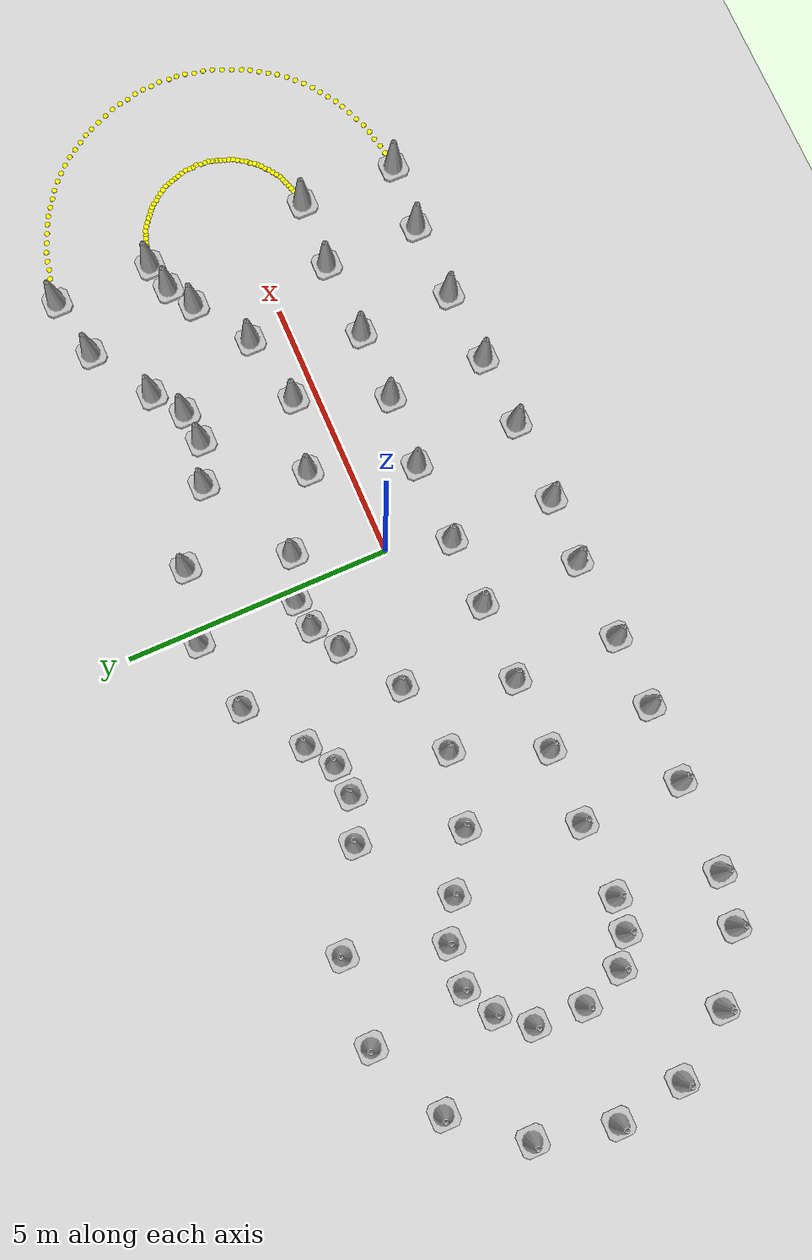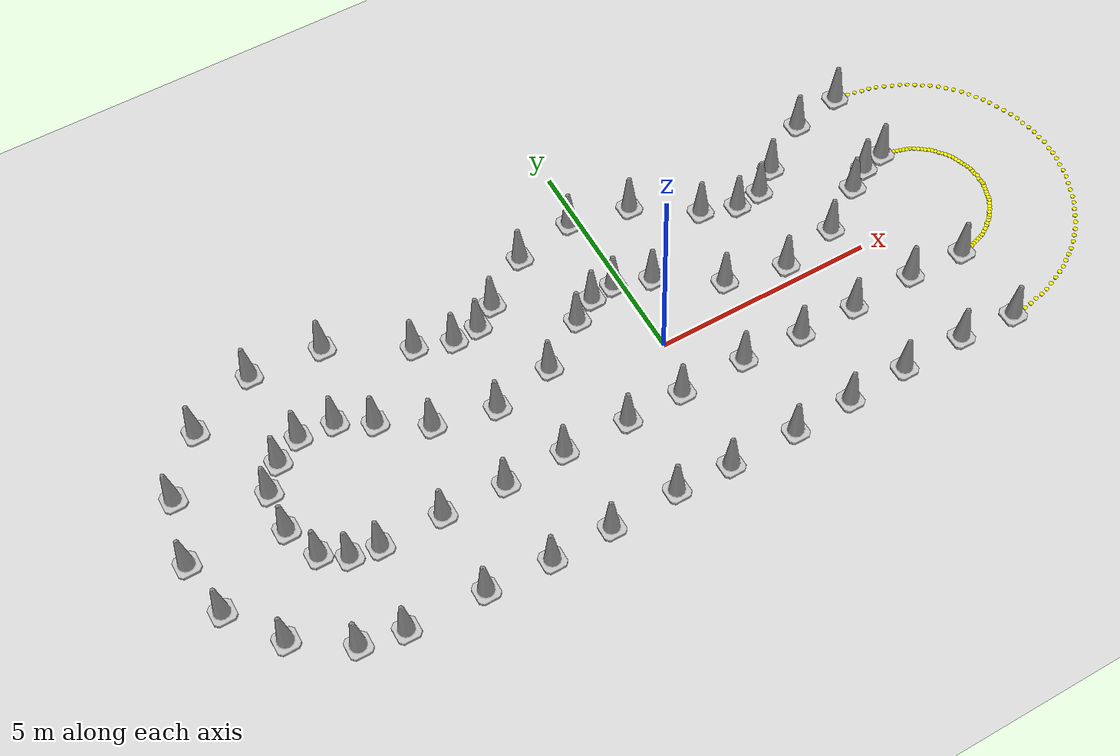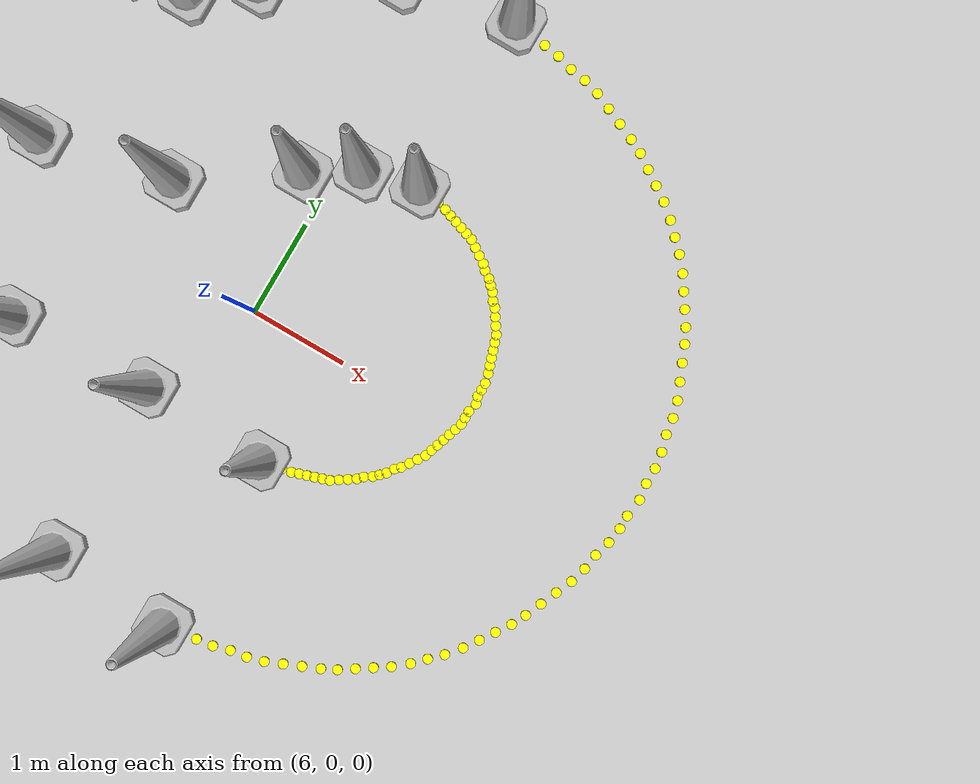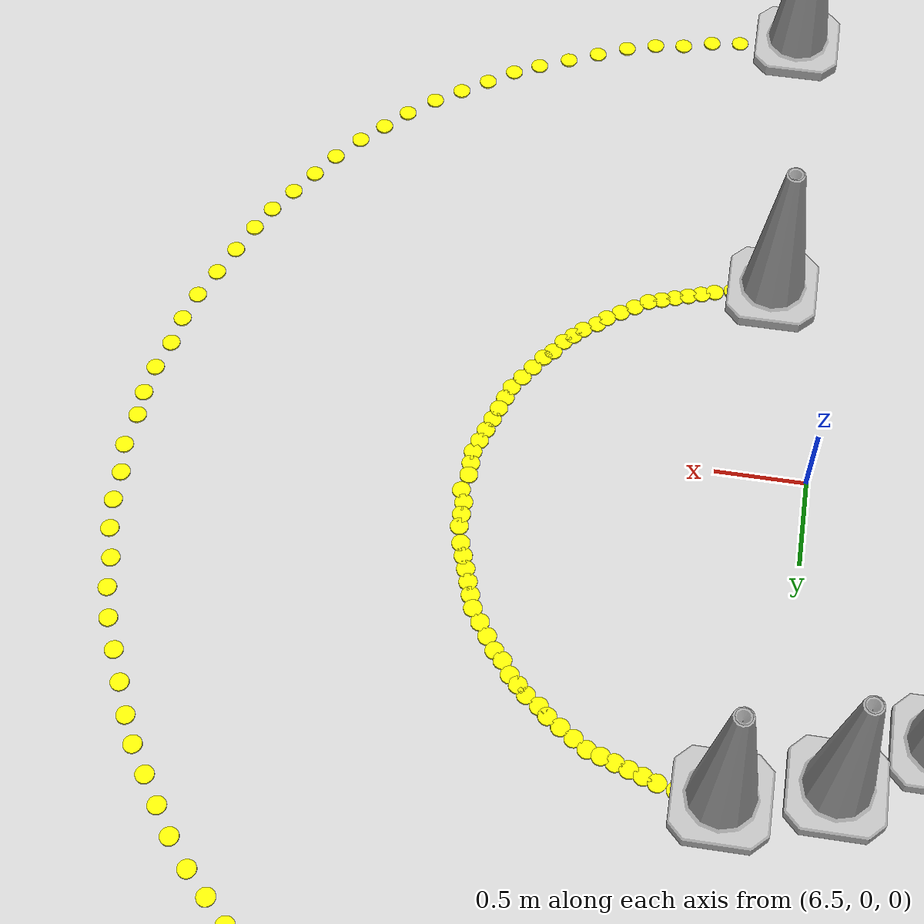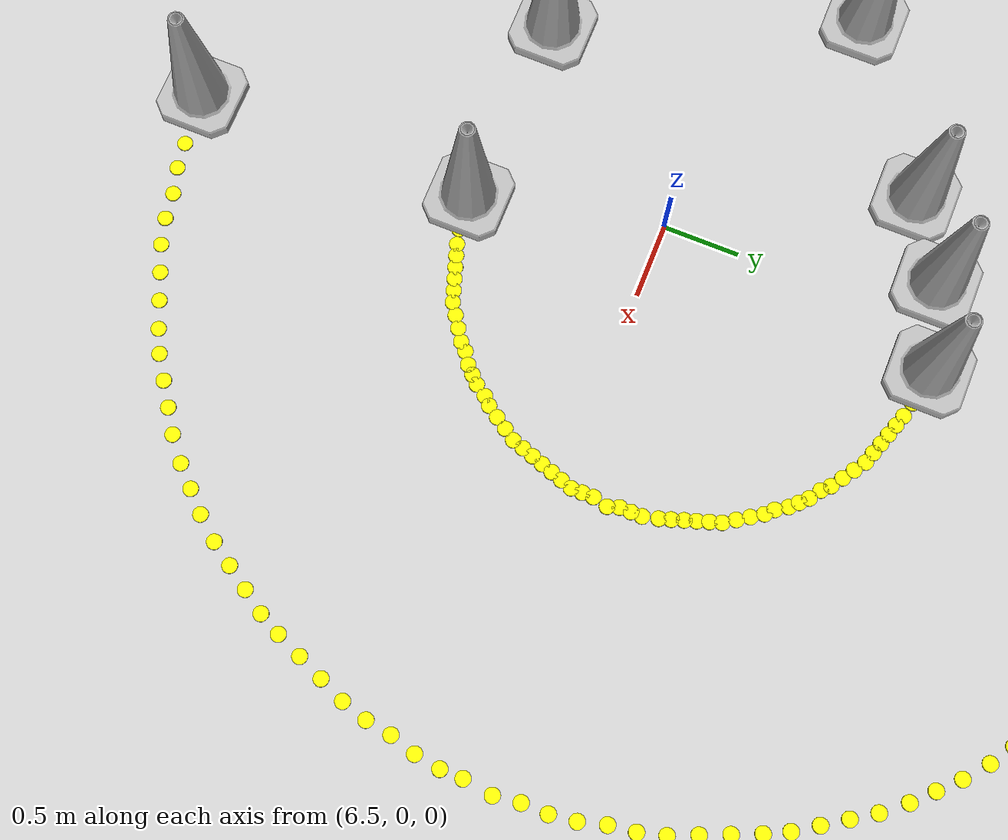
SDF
<sdf version="1.6">
 <world name="default">
  <light name="sun" type="directional">
   <pose>0 0 10 0 -0 0</pose>
   <diffuse>0.8 0.8 0.8 1</diffuse>
   <specular>0.2 0.2 0.2 1</specular>
   <attenuation>
    <range>1000</range>
    <constant>0.9</constant>
    <linear>0.01</linear>
    <quadratic>0.001</quadratic>
   </attenuation>
   <direction>-0.5 0.1 -0.9</direction>
  </light>
  <model name="ground_plane">
   <static>1</static>
   <link name="link">
    <collision name="collision">
     <geometry><plane><normal>0 0 1</normal><size>100 100</size></plane></geometry>
     <surface><friction><ode><mu>100</mu><mu2>50</mu2></ode></friction></surface>
    </collision>
    <visual name="visual">
     <cast_shadows>0</cast_shadows>
     <geometry><plane><normal>0 0 1</normal><size>100 100</size></plane></geometry>
     <material>
      <script><uri>file://media/materials/scripts/gazebo.material</uri><name>Gazebo/Grey</name></script>
     </material>
    </visual>
   </link>
  </model>
  <gravity>0 0 -9.8</gravity>
  <magnetic_field>6e-06 2.3e-05 -4.2e-05</magnetic_field>
  <atmosphere type="adiabatic"/>
  <physics name="default_physics" default="0" type="ode">
   <max_step_size>0.001</max_step_size>
   <real_time_factor>1</real_time_factor>
   <real_time_update_rate>1000</real_time_update_rate>
  </physics>
  <scene><ambient>0.4 0.4 0.4 1</ambient><background>0.7 0.7 0.7 1</background><shadows>1</shadows></scene>
  <audio><device>default</device></audio>
  <spherical_coordinates>
   <surface_model>EARTH_WGS84</surface_model>
   <latitude_deg>0</latitude_deg>
   <longitude_deg>0</longitude_deg>
   <elevation>0</elevation>
   <heading_deg>0</heading_deg>
  </spherical_coordinates>
  <model name="red_model_1">
   <link name="link">
    <collision name="collision">
     <geometry>
      <mesh><scale>10 10 10</scale><uri>model://construction_cone_red/meshes/construction_cone.dae</uri></mesh>
     </geometry>
    </collision>
    <visual name="visual">
     <geometry>
      <mesh><scale>10 10 10</scale><uri>model://construction_cone_red/meshes/construction_cone.dae</uri></mesh>
     </geometry>
    </visual>
    <inertial>
     <inertia><ixx>1</ixx><ixy>0</ixy><ixz>0</ixz><iyy>1</iyy><iyz>0</iyz><izz>1</izz></inertia>
     <mass>1</mass>
    </inertial>
   </link>
   <pose>6.78955 -1.23001 0.004999 0 -0 0.000331</pose>
  </model>
  <model name="red_model_2">
   <link name="link">
    <collision name="collision">
     <geometry>
      <mesh><scale>10 10 10</scale><uri>model://construction_cone_red/meshes/construction_cone.dae</uri></mesh>
     </geometry>
    </collision>
    <visual name="visual">
     <geometry>
      <mesh><scale>10 10 10</scale><uri>model://construction_cone_red/meshes/construction_cone.dae</uri></mesh>
     </geometry>
    </visual>
    <inertial>
     <inertia><ixx>1</ixx><ixy>0</ixy><ixz>0</ixz><iyy>1</iyy><iyz>0</iyz><izz>1</izz></inertia>
     <mass>1</mass>
    </inertial>
   </link>
   <pose>3.9852 -1.23 -0 0 -1e-06 0</pose>
  </model>
  <model name="red_model_3">
   <link name="link">
    <collision name="collision">
     <geometry>
      <mesh><scale>10 10 10</scale><uri>model://construction_cone_red/meshes/construction_cone.dae</uri></mesh>
     </geometry>
    </collision>
    <visual name="visual">
     <geometry>
      <mesh><scale>10 10 10</scale><uri>model://construction_cone_red/meshes/construction_cone.dae</uri></mesh>
     </geometry>
    </visual>
    <inertial>
     <inertia><ixx>1</ixx><ixy>0</ixy><ixz>0</ixz><iyy>1</iyy><iyz>0</iyz><izz>1</izz></inertia>
     <mass>1</mass>
    </inertial>
   </link>
   <pose>2.6322 -1.23 -0 0 -1e-06 0</pose>
  </model>
  <model name="red_model_4">
   <link name="link">
    <collision name="collision">
     <geometry>
      <mesh><scale>10 10 10</scale><uri>model://construction_cone_red/meshes/construction_cone.dae</uri></mesh>
     </geometry>
    </collision>
    <visual name="visual">
     <geometry>
      <mesh><scale>10 10 10</scale><uri>model://construction_cone_red/meshes/construction_cone.dae</uri></mesh>
     </geometry>
    </visual>
    <inertial>
     <inertia><ixx>1</ixx><ixy>0</ixy><ixz>0</ixz><iyy>1</iyy><iyz>0</iyz><izz>1</izz></inertia>
     <mass>1</mass>
    </inertial>
   </link>
   <pose>1.2546 -1.1562 -0 0 -1e-06 0</pose>
  </model>
  <model name="red_model_5">
   <link name="link">
    <collision name="collision">
     <geometry>
      <mesh><scale>10 10 10</scale><uri>model://construction_cone_red/meshes/construction_cone.dae</uri></mesh>
     </geometry>
    </collision>
    <visual name="visual">
     <geometry>
      <mesh><scale>10 10 10</scale><uri>model://construction_cone_red/meshes/construction_cone.dae</uri></mesh>
     </geometry>
    </visual>
    <inertial>
     <inertia><ixx>1</ixx><ixy>0</ixy><ixz>0</ixz><iyy>1</iyy><iyz>0</iyz><izz>1</izz></inertia>
     <mass>1</mass>
    </inertial>
   </link>
   <pose>-0.2706 -1.1808 -0 0 -0 0</pose>
  </model>
  <model name="red_model_6">
   <link name="link">
    <collision name="collision">
     <geometry>
      <mesh><scale>10 10 10</scale><uri>model://construction_cone_red/meshes/construction_cone.dae</uri></mesh>
     </geometry>
    </collision>
    <visual name="visual">
     <geometry>
      <mesh><scale>10 10 10</scale><uri>model://construction_cone_red/meshes/construction_cone.dae</uri></mesh>
     </geometry>
    </visual>
    <inertial>
     <inertia><ixx>1</ixx><ixy>0</ixy><ixz>0</ixz><iyy>1</iyy><iyz>0</iyz><izz>1</izz></inertia>
     <mass>1</mass>
    </inertial>
   </link>
   <pose>-1.5744 -1.2054 -0 0 -1e-06 0</pose>
  </model>
  <model name="red_model_7">
   <link name="link">
    <collision name="collision">
     <geometry>
      <mesh><scale>10 10 10</scale><uri>model://construction_cone_red/meshes/construction_cone.dae</uri></mesh>
     </geometry>
    </collision>
    <visual name="visual">
     <geometry>
      <mesh><scale>10 10 10</scale><uri>model://construction_cone_red/meshes/construction_cone.dae</uri></mesh>
     </geometry>
    </visual>
    <inertial>
     <inertia><ixx>1</ixx><ixy>0</ixy><ixz>0</ixz><iyy>1</iyy><iyz>0</iyz><izz>1</izz></inertia>
     <mass>1</mass>
    </inertial>
   </link>
   <pose>-3.0504 -1.1808 -0 0 -1e-06 0</pose>
  </model>
  <model name="red_model_8">
   <link name="link">
    <collision name="collision">
     <geometry>
      <mesh><scale>10 10 10</scale><uri>model://construction_cone_red/meshes/construction_cone.dae</uri></mesh>
     </geometry>
    </collision>
    <visual name="visual">
     <geometry>
      <mesh><scale>10 10 10</scale><uri>model://construction_cone_red/meshes/construction_cone.dae</uri></mesh>
     </geometry>
    </visual>
    <inertial>
     <inertia><ixx>1</ixx><ixy>0</ixy><ixz>0</ixz><iyy>1</iyy><iyz>0</iyz><izz>1</izz></inertia>
     <mass>1</mass>
    </inertial>
   </link>
   <pose>-4.428 -1.23 -0 0 -1e-06 0</pose>
  </model>
  <model name="red_model_9">
   <link name="link">
    <collision name="collision">
     <geometry>
      <mesh><scale>10 10 10</scale><uri>model://construction_cone_red/meshes/construction_cone.dae</uri></mesh>
     </geometry>
    </collision>
    <visual name="visual">
     <geometry>
      <mesh><scale>10 10 10</scale><uri>model://construction_cone_red/meshes/construction_cone.dae</uri></mesh>
     </geometry>
    </visual>
    <inertial>
     <inertia><ixx>1</ixx><ixy>0</ixy><ixz>0</ixz><iyy>1</iyy><iyz>0</iyz><izz>1</izz></inertia>
     <mass>1</mass>
    </inertial>
   </link>
   <pose>-5.8302 -1.2054 -0 0 -1e-06 0</pose>
  </model>
  <model name="red_model_10">
   <link name="link">
    <collision name="collision">
     <geometry>
      <mesh><scale>10 10 10</scale><uri>model://construction_cone_red/meshes/construction_cone.dae</uri></mesh>
     </geometry>
    </collision>
    <visual name="visual">
     <geometry>
      <mesh><scale>10 10 10</scale><uri>model://construction_cone_red/meshes/construction_cone.dae</uri></mesh>
     </geometry>
    </visual>
    <inertial>
     <inertia><ixx>1</ixx><ixy>0</ixy><ixz>0</ixz><iyy>1</iyy><iyz>0</iyz><izz>1</izz></inertia>
     <mass>1</mass>
    </inertial>
   </link>
   <pose>-7.2078 -1.2054 -0 0 -1e-06 0</pose>
  </model>
  <model name="red_model_11">
   <link name="link">
    <collision name="collision">
     <geometry>
      <mesh><scale>10 10 10</scale><uri>model://construction_cone_red/meshes/construction_cone.dae</uri></mesh>
     </geometry>
    </collision>
    <visual name="visual">
     <geometry>
      <mesh><scale>10 10 10</scale><uri>model://construction_cone_red/meshes/construction_cone.dae</uri></mesh>
     </geometry>
    </visual>
    <inertial>
     <inertia><ixx>1</ixx><ixy>0</ixy><ixz>0</ixz><iyy>1</iyy><iyz>0</iyz><izz>1</izz></inertia>
     <mass>1</mass>
    </inertial>
   </link>
   <pose>-7.8228 -1.107 -0 0 -1e-06 0</pose>
  </model>
  <model name="red_model_12">
   <link name="link">
    <collision name="collision">
     <geometry>
      <mesh><scale>10 10 10</scale><uri>model://construction_cone_red/meshes/construction_cone.dae</uri></mesh>
     </geometry>
    </collision>
    <visual name="visual">
     <geometry>
      <mesh><scale>10 10 10</scale><uri>model://construction_cone_red/meshes/construction_cone.dae</uri></mesh>
     </geometry>
    </visual>
    <inertial>
     <inertia><ixx>1</ixx><ixy>0</ixy><ixz>0</ixz><iyy>1</iyy><iyz>0</iyz><izz>1</izz></inertia>
     <mass>1</mass>
    </inertial>
   </link>
   <pose>-8.3394 -0.7626 -8e-06 1e-06 -0 0</pose>
  </model>
  <model name="red_model_13">
   <link name="link">
    <collision name="collision">
     <geometry>
      <mesh><scale>10 10 10</scale><uri>model://construction_cone_red/meshes/construction_cone.dae</uri></mesh>
     </geometry>
    </collision>
    <visual name="visual">
     <geometry>
      <mesh><scale>10 10 10</scale><uri>model://construction_cone_red/meshes/construction_cone.dae</uri></mesh>
     </geometry>
    </visual>
    <inertial>
     <inertia><ixx>1</ixx><ixy>0</ixy><ixz>0</ixz><iyy>1</iyy><iyz>0</iyz><izz>1</izz></inertia>
     <mass>1</mass>
    </inertial>
   </link>
   <pose>3.321 0.4182 -0 0 -0 0</pose>
  </model>
  <model name="red_model_14">
   <link name="link">
    <collision name="collision">
     <geometry>
      <mesh><scale>10 10 10</scale><uri>model://construction_cone_red/meshes/construction_cone.dae</uri></mesh>
     </geometry>
    </collision>
    <visual name="visual">
     <geometry>
      <mesh><scale>10 10 10</scale><uri>model://construction_cone_red/meshes/construction_cone.dae</uri></mesh>
     </geometry>
    </visual>
    <inertial>
     <inertia><ixx>1</ixx><ixy>0</ixy><ixz>0</ixz><iyy>1</iyy><iyz>0</iyz><izz>1</izz></inertia>
     <mass>1</mass>
    </inertial>
   </link>
   <pose>-8.6592 0.0492 -0 0 -1e-06 0</pose>
  </model>
  <model name="red_model_15">
   <link name="link">
    <collision name="collision">
     <geometry>
      <mesh><scale>10 10 10</scale><uri>model://construction_cone_red/meshes/construction_cone.dae</uri></mesh>
     </geometry>
    </collision>
    <visual name="visual">
     <geometry>
      <mesh><scale>10 10 10</scale><uri>model://construction_cone_red/meshes/construction_cone.dae</uri></mesh>
     </geometry>
    </visual>
    <inertial>
     <inertia><ixx>1</ixx><ixy>0</ixy><ixz>0</ixz><iyy>1</iyy><iyz>0</iyz><izz>1</izz></inertia>
     <mass>1</mass>
    </inertial>
   </link>
   <pose>-3.7392 0.4182 0 -0 -0 -0</pose>
  </model>
  <model name="red_model_16">
   <link name="link">
    <collision name="collision">
     <geometry>
      <mesh><scale>10 10 10</scale><uri>model://construction_cone_red/meshes/construction_cone.dae</uri></mesh>
     </geometry>
    </collision>
    <visual name="visual">
     <geometry>
      <mesh><scale>10 10 10</scale><uri>model://construction_cone_red/meshes/construction_cone.dae</uri></mesh>
     </geometry>
    </visual>
    <inertial>
     <inertia><ixx>1</ixx><ixy>0</ixy><ixz>0</ixz><iyy>1</iyy><iyz>0</iyz><izz>1</izz></inertia>
     <mass>1</mass>
    </inertial>
   </link>
   <pose>4.674 0.7134 -0 0 -1e-06 0</pose>
  </model>
  <model name="red_model_17">
   <link name="link">
    <collision name="collision">
     <geometry>
      <mesh><scale>10 10 10</scale><uri>model://construction_cone_red/meshes/construction_cone.dae</uri></mesh>
     </geometry>
    </collision>
    <visual name="visual">
     <geometry>
      <mesh><scale>10 10 10</scale><uri>model://construction_cone_red/meshes/construction_cone.dae</uri></mesh>
     </geometry>
    </visual>
    <inertial>
     <inertia><ixx>1</ixx><ixy>0</ixy><ixz>0</ixz><iyy>1</iyy><iyz>0</iyz><izz>1</izz></inertia>
     <mass>1</mass>
    </inertial>
   </link>
   <pose>1.9434 0.7134 -0 0 -1e-06 0</pose>
  </model>
  <model name="red_model_18">
   <link name="link">
    <collision name="collision">
     <geometry>
      <mesh><scale>10 10 10</scale><uri>model://construction_cone_red/meshes/construction_cone.dae</uri></mesh>
     </geometry>
    </collision>
    <visual name="visual">
     <geometry>
      <mesh><scale>10 10 10</scale><uri>model://construction_cone_red/meshes/construction_cone.dae</uri></mesh>
     </geometry>
    </visual>
    <inertial>
     <inertia><ixx>1</ixx><ixy>0</ixy><ixz>0</ixz><iyy>1</iyy><iyz>0</iyz><izz>1</izz></inertia>
     <mass>1</mass>
    </inertial>
   </link>
   <pose>-2.3616 0.7134 -0 0 -1e-06 0</pose>
  </model>
  <model name="red_model_19">
   <link name="link">
    <collision name="collision">
     <geometry>
      <mesh><scale>10 10 10</scale><uri>model://construction_cone_red/meshes/construction_cone.dae</uri></mesh>
     </geometry>
    </collision>
    <visual name="visual">
     <geometry>
      <mesh><scale>10 10 10</scale><uri>model://construction_cone_red/meshes/construction_cone.dae</uri></mesh>
     </geometry>
    </visual>
    <inertial>
     <inertia><ixx>1</ixx><ixy>0</ixy><ixz>0</ixz><iyy>1</iyy><iyz>0</iyz><izz>1</izz></inertia>
     <mass>1</mass>
    </inertial>
   </link>
   <pose>-5.0922 0.7134 -9e-06 0 -0 0</pose>
  </model>
  <model name="red_model_20">
   <link name="link">
    <collision name="collision">
     <geometry>
      <mesh><scale>10 10 10</scale><uri>model://construction_cone_red/meshes/construction_cone.dae</uri></mesh>
     </geometry>
    </collision>
    <visual name="visual">
     <geometry>
      <mesh><scale>10 10 10</scale><uri>model://construction_cone_red/meshes/construction_cone.dae</uri></mesh>
     </geometry>
    </visual>
    <inertial>
     <inertia><ixx>1</ixx><ixy>0</ixy><ixz>0</ixz><iyy>1</iyy><iyz>0</iyz><izz>1</izz></inertia>
     <mass>1</mass>
    </inertial>
   </link>
   <pose>-8.61 0.984 -0 0 -1e-06 0</pose>
  </model>
  <model name="red_model_21">
   <link name="link">
    <collision name="collision">
     <geometry>
      <mesh><scale>10 10 10</scale><uri>model://construction_cone_red/meshes/construction_cone.dae</uri></mesh>
     </geometry>
    </collision>
    <visual name="visual">
     <geometry>
      <mesh><scale>10 10 10</scale><uri>model://construction_cone_red/meshes/construction_cone.dae</uri></mesh>
     </geometry>
    </visual>
    <inertial>
     <inertia><ixx>1</ixx><ixy>0</ixy><ixz>0</ixz><iyy>1</iyy><iyz>0</iyz><izz>1</izz></inertia>
     <mass>1</mass>
    </inertial>
   </link>
   <pose>-1.2792 1.4514 -9e-06 0 -0 0</pose>
  </model>
  <model name="red_model_22">
   <link name="link">
    <collision name="collision">
     <geometry>
      <mesh><scale>10 10 10</scale><uri>model://construction_cone_red/meshes/construction_cone.dae</uri></mesh>
     </geometry>
    </collision>
    <visual name="visual">
     <geometry>
      <mesh><scale>10 10 10</scale><uri>model://construction_cone_red/meshes/construction_cone.dae</uri></mesh>
     </geometry>
    </visual>
    <inertial>
     <inertia><ixx>1</ixx><ixy>0</ixy><ixz>0</ixz><iyy>1</iyy><iyz>0</iyz><izz>1</izz></inertia>
     <mass>1</mass>
    </inertial>
   </link>
   <pose>-6.0762 1.353 -0 0 -1e-06 0</pose>
  </model>
  <model name="red_model_23">
   <link name="link">
    <collision name="collision">
     <geometry>
      <mesh><scale>10 10 10</scale><uri>model://construction_cone_red/meshes/construction_cone.dae</uri></mesh>
     </geometry>
    </collision>
    <visual name="visual">
     <geometry>
      <mesh><scale>10 10 10</scale><uri>model://construction_cone_red/meshes/construction_cone.dae</uri></mesh>
     </geometry>
    </visual>
    <inertial>
     <inertia><ixx>1</ixx><ixy>0</ixy><ixz>0</ixz><iyy>1</iyy><iyz>0</iyz><izz>1</izz></inertia>
     <mass>1</mass>
    </inertial>
   </link>
   <pose>5.72569 1.42144 -9.8e-05 0 -0 -0.000104</pose>
  </model>
  <model name="red_model_24">
   <link name="link">
    <collision name="collision">
     <geometry>
      <mesh><scale>10 10 10</scale><uri>model://construction_cone_red/meshes/construction_cone.dae</uri></mesh>
     </geometry>
    </collision>
    <visual name="visual">
     <geometry>
      <mesh><scale>10 10 10</scale><uri>model://construction_cone_red/meshes/construction_cone.dae</uri></mesh>
     </geometry>
    </visual>
    <inertial>
     <inertia><ixx>1</ixx><ixy>0</ixy><ixz>0</ixz><iyy>1</iyy><iyz>0</iyz><izz>1</izz></inertia>
     <mass>1</mass>
    </inertial>
   </link>
   <pose>-8.1672 1.5252 -0 0 -0 0</pose>
  </model>
  <model name="red_model_25">
   <link name="link">
    <collision name="collision">
     <geometry>
      <mesh><scale>10 10 10</scale><uri>model://construction_cone_red/meshes/construction_cone.dae</uri></mesh>
     </geometry>
    </collision>
    <visual name="visual">
     <geometry>
      <mesh><scale>10 10 10</scale><uri>model://construction_cone_red/meshes/construction_cone.dae</uri></mesh>
     </geometry>
    </visual>
    <inertial>
     <inertia><ixx>1</ixx><ixy>0</ixy><ixz>0</ixz><iyy>1</iyy><iyz>0</iyz><izz>1</izz></inertia>
     <mass>1</mass>
    </inertial>
   </link>
   <pose>0.6396 1.5744 -0 0 -1e-06 0</pose>
  </model>
  <model name="red_model_26">
   <link name="link">
    <collision name="collision">
     <geometry>
      <mesh><scale>10 10 10</scale><uri>model://construction_cone_red/meshes/construction_cone.dae</uri></mesh>
     </geometry>
    </collision>
    <visual name="visual">
     <geometry>
      <mesh><scale>10 10 10</scale><uri>model://construction_cone_red/meshes/construction_cone.dae</uri></mesh>
     </geometry>
    </visual>
    <inertial>
     <inertia><ixx>1</ixx><ixy>0</ixy><ixz>0</ixz><iyy>1</iyy><iyz>0</iyz><izz>1</izz></inertia>
     <mass>1</mass>
    </inertial>
   </link>
   <pose>-0.738 1.7712 -0 0 -0 0</pose>
  </model>
  <model name="red_model_27">
   <link name="link">
    <collision name="collision">
     <geometry>
      <mesh><scale>10 10 10</scale><uri>model://construction_cone_red/meshes/construction_cone.dae</uri></mesh>
     </geometry>
    </collision>
    <visual name="visual">
     <geometry>
      <mesh><scale>10 10 10</scale><uri>model://construction_cone_red/meshes/construction_cone.dae</uri></mesh>
     </geometry>
    </visual>
    <inertial>
     <inertia><ixx>1</ixx><ixy>0</ixy><ixz>0</ixz><iyy>1</iyy><iyz>0</iyz><izz>1</izz></inertia>
     <mass>1</mass>
    </inertial>
   </link>
   <pose>6.22901 1.72751 0.003913 0.00262 -0.013788 0.0036</pose>
  </model>
  <model name="red_model_28">
   <link name="link">
    <collision name="collision">
     <geometry>
      <mesh><scale>10 10 10</scale><uri>model://construction_cone_red/meshes/construction_cone.dae</uri></mesh>
     </geometry>
    </collision>
    <visual name="visual">
     <geometry>
      <mesh><scale>10 10 10</scale><uri>model://construction_cone_red/meshes/construction_cone.dae</uri></mesh>
     </geometry>
    </visual>
    <inertial>
     <inertia><ixx>1</ixx><ixy>0</ixy><ixz>0</ixz><iyy>1</iyy><iyz>0</iyz><izz>1</izz></inertia>
     <mass>1</mass>
    </inertial>
   </link>
   <pose>-6.7896 1.7712 -0 0 -1e-06 0</pose>
  </model>
  <model name="red_model_29">
   <link name="link">
    <collision name="collision">
     <geometry>
      <mesh><scale>10 10 10</scale><uri>model://construction_cone_red/meshes/construction_cone.dae</uri></mesh>
     </geometry>
    </collision>
    <visual name="visual">
     <geometry>
      <mesh><scale>10 10 10</scale><uri>model://construction_cone_red/meshes/construction_cone.dae</uri></mesh>
     </geometry>
    </visual>
    <inertial>
     <inertia><ixx>1</ixx><ixy>0</ixy><ixz>0</ixz><iyy>1</iyy><iyz>0</iyz><izz>1</izz></inertia>
     <mass>1</mass>
    </inertial>
   </link>
   <pose>-7.5768 1.845 -0 0 -1e-06 0</pose>
  </model>
  <model name="red_model_30">
   <link name="link">
    <collision name="collision">
     <geometry>
      <mesh><scale>10 10 10</scale><uri>model://construction_cone_red/meshes/construction_cone.dae</uri></mesh>
     </geometry>
    </collision>
    <visual name="visual">
     <geometry>
      <mesh><scale>10 10 10</scale><uri>model://construction_cone_red/meshes/construction_cone.dae</uri></mesh>
     </geometry>
    </visual>
    <inertial>
     <inertia><ixx>1</ixx><ixy>0</ixy><ixz>0</ixz><iyy>1</iyy><iyz>0</iyz><izz>1</izz></inertia>
     <mass>1</mass>
    </inertial>
   </link>
   <pose>6.7896 1.8696 0.00499 0 -0 5e-06</pose>
  </model>
  <model name="red_model_31">
   <link name="link">
    <collision name="collision">
     <geometry>
      <mesh><scale>10 10 10</scale><uri>model://construction_cone_red/meshes/construction_cone.dae</uri></mesh>
     </geometry>
    </collision>
    <visual name="visual">
     <geometry>
      <mesh><scale>10 10 10</scale><uri>model://construction_cone_red/meshes/construction_cone.dae</uri></mesh>
     </geometry>
    </visual>
    <inertial>
     <inertia><ixx>1</ixx><ixy>0</ixy><ixz>0</ixz><iyy>1</iyy><iyz>0</iyz><izz>1</izz></inertia>
     <mass>1</mass>
    </inertial>
   </link>
   <pose>-0.1722 1.845 -0 -0 -0 -0</pose>
  </model>
  <model name="blue_model_0">
   <link name="link">
    <collision name="collision">
     <geometry>
      <mesh><scale>10 10 10</scale><uri>model://construction_cone_blue/meshes/construction_cone.dae</uri></mesh>
     </geometry>
    </collision>
    <visual name="visual">
     <geometry>
      <mesh><scale>10 10 10</scale><uri>model://construction_cone_blue/meshes/construction_cone.dae</uri></mesh>
     </geometry>
    </visual>
    <inertial>
     <inertia><ixx>1</ixx><ixy>0</ixy><ixz>0</ixz><iyy>1</iyy><iyz>0</iyz><izz>1</izz></inertia>
     <mass>1</mass>
    </inertial>
   </link>
   <pose>1.2546 -3.1488 -8e-06 1e-06 -0 0</pose>
  </model>
  <model name="blue_model_1">
   <link name="link">
    <collision name="collision">
     <geometry>
      <mesh><scale>10 10 10</scale><uri>model://construction_cone_blue/meshes/construction_cone.dae</uri></mesh>
     </geometry>
    </collision>
    <visual name="visual">
     <geometry>
      <mesh><scale>10 10 10</scale><uri>model://construction_cone_blue/meshes/construction_cone.dae</uri></mesh>
     </geometry>
    </visual>
    <inertial>
     <inertia><ixx>1</ixx><ixy>0</ixy><ixz>0</ixz><iyy>1</iyy><iyz>0</iyz><izz>1</izz></inertia>
     <mass>1</mass>
    </inertial>
   </link>
   <pose>-0.2952 -3.1488 -0 0 -1e-06 0</pose>
  </model>
  <model name="blue_model_2">
   <link name="link">
    <collision name="collision">
     <geometry>
      <mesh><scale>10 10 10</scale><uri>model://construction_cone_blue/meshes/construction_cone.dae</uri></mesh>
     </geometry>
    </collision>
    <visual name="visual">
     <geometry>
      <mesh><scale>10 10 10</scale><uri>model://construction_cone_blue/meshes/construction_cone.dae</uri></mesh>
     </geometry>
    </visual>
    <inertial>
     <inertia><ixx>1</ixx><ixy>0</ixy><ixz>0</ixz><iyy>1</iyy><iyz>0</iyz><izz>1</izz></inertia>
     <mass>1</mass>
    </inertial>
   </link>
   <pose>-3.075 -3.1488 -0 0 -1e-06 0</pose>
  </model>
  <model name="blue_model_3">
   <link name="link">
    <collision name="collision">
     <geometry>
      <mesh><scale>10 10 10</scale><uri>model://construction_cone_blue/meshes/construction_cone.dae</uri></mesh>
     </geometry>
    </collision>
    <visual name="visual">
     <geometry>
      <mesh><scale>10 10 10</scale><uri>model://construction_cone_blue/meshes/construction_cone.dae</uri></mesh>
     </geometry>
    </visual>
    <inertial>
     <inertia><ixx>1</ixx><ixy>0</ixy><ixz>0</ixz><iyy>1</iyy><iyz>0</iyz><izz>1</izz></inertia>
     <mass>1</mass>
    </inertial>
   </link>
   <pose>6.7896 -3.0996 0.004993 0 -0 2.9e-05</pose>
  </model>
  <model name="blue_model_4">
   <link name="link">
    <collision name="collision">
     <geometry>
      <mesh><scale>10 10 10</scale><uri>model://construction_cone_blue/meshes/construction_cone.dae</uri></mesh>
     </geometry>
    </collision>
    <visual name="visual">
     <geometry>
      <mesh><scale>10 10 10</scale><uri>model://construction_cone_blue/meshes/construction_cone.dae</uri></mesh>
     </geometry>
    </visual>
    <inertial>
     <inertia><ixx>1</ixx><ixy>0</ixy><ixz>0</ixz><iyy>1</iyy><iyz>0</iyz><izz>1</izz></inertia>
     <mass>1</mass>
    </inertial>
   </link>
   <pose>2.6322 -3.0996 -0 0 -1e-06 0</pose>
  </model>
  <model name="blue_model_5">
   <link name="link">
    <collision name="collision">
     <geometry>
      <mesh><scale>10 10 10</scale><uri>model://construction_cone_blue/meshes/construction_cone.dae</uri></mesh>
     </geometry>
    </collision>
    <visual name="visual">
     <geometry>
      <mesh><scale>10 10 10</scale><uri>model://construction_cone_blue/meshes/construction_cone.dae</uri></mesh>
     </geometry>
    </visual>
    <inertial>
     <inertia><ixx>1</ixx><ixy>0</ixy><ixz>0</ixz><iyy>1</iyy><iyz>0</iyz><izz>1</izz></inertia>
     <mass>1</mass>
    </inertial>
   </link>
   <pose>-4.42764 -3.17179 -0 0 0 -0.003223</pose>
  </model>
  <model name="blue_model_6">
   <link name="link">
    <collision name="collision">
     <geometry>
      <mesh><scale>10 10 10</scale><uri>model://construction_cone_blue/meshes/construction_cone.dae</uri></mesh>
     </geometry>
    </collision>
    <visual name="visual">
     <geometry>
      <mesh><scale>10 10 10</scale><uri>model://construction_cone_blue/meshes/construction_cone.dae</uri></mesh>
     </geometry>
    </visual>
    <inertial>
     <inertia><ixx>1</ixx><ixy>0</ixy><ixz>0</ixz><iyy>1</iyy><iyz>0</iyz><izz>1</izz></inertia>
     <mass>1</mass>
    </inertial>
   </link>
   <pose>-5.8548 -3.0996 -0 0 -0 0</pose>
  </model>
  <model name="blue_model_7">
   <link name="link">
    <collision name="collision">
     <geometry>
      <mesh><scale>10 10 10</scale><uri>model://construction_cone_blue/meshes/construction_cone.dae</uri></mesh>
     </geometry>
    </collision>
    <visual name="visual">
     <geometry>
      <mesh><scale>10 10 10</scale><uri>model://construction_cone_blue/meshes/construction_cone.dae</uri></mesh>
     </geometry>
    </visual>
    <inertial>
     <inertia><ixx>1</ixx><ixy>0</ixy><ixz>0</ixz><iyy>1</iyy><iyz>0</iyz><izz>1</izz></inertia>
     <mass>1</mass>
    </inertial>
   </link>
   <pose>-7.5522 -3.0504 -0 0 -1e-06 0</pose>
  </model>
  <model name="blue_model_8">
   <link name="link">
    <collision name="collision">
     <geometry>
      <mesh><scale>10 10 10</scale><uri>model://construction_cone_blue/meshes/construction_cone.dae</uri></mesh>
     </geometry>
    </collision>
    <visual name="visual">
     <geometry>
      <mesh><scale>10 10 10</scale><uri>model://construction_cone_blue/meshes/construction_cone.dae</uri></mesh>
     </geometry>
    </visual>
    <inertial>
     <inertia><ixx>1</ixx><ixy>0</ixy><ixz>0</ixz><iyy>1</iyy><iyz>0</iyz><izz>1</izz></inertia>
     <mass>1</mass>
    </inertial>
   </link>
   <pose>-8.487 -2.8782 -0 0 -1e-06 0</pose>
  </model>
  <model name="blue_model_11">
   <link name="link">
    <collision name="collision">
     <geometry>
      <mesh><scale>10 10 10</scale><uri>model://construction_cone_blue/meshes/construction_cone.dae</uri></mesh>
     </geometry>
    </collision>
    <visual name="visual">
     <geometry>
      <mesh><scale>10 10 10</scale><uri>model://construction_cone_blue/meshes/construction_cone.dae</uri></mesh>
     </geometry>
    </visual>
    <inertial>
     <inertia><ixx>1</ixx><ixy>0</ixy><ixz>0</ixz><iyy>1</iyy><iyz>0</iyz><izz>1</izz></inertia>
     <mass>1</mass>
    </inertial>
   </link>
   <pose>-9.6432 -2.091 -1e-05 -0 -0 -0</pose>
  </model>
  <model name="blue_model_13">
   <link name="link">
    <collision name="collision">
     <geometry>
      <mesh><scale>10 10 10</scale><uri>model://construction_cone_blue/meshes/construction_cone.dae</uri></mesh>
     </geometry>
    </collision>
    <visual name="visual">
     <geometry>
      <mesh><scale>10 10 10</scale><uri>model://construction_cone_blue/meshes/construction_cone.dae</uri></mesh>
     </geometry>
    </visual>
    <inertial>
     <inertia><ixx>1</ixx><ixy>0</ixy><ixz>0</ixz><iyy>1</iyy><iyz>0</iyz><izz>1</izz></inertia>
     <mass>1</mass>
    </inertial>
   </link>
   <pose>-10.455 -0.9348 -0 0 -1e-06 0</pose>
  </model>
  <model name="blue_model_14">
   <link name="link">
    <collision name="collision">
     <geometry>
      <mesh><scale>10 10 10</scale><uri>model://construction_cone_blue/meshes/construction_cone.dae</uri></mesh>
     </geometry>
    </collision>
    <visual name="visual">
     <geometry>
      <mesh><scale>10 10 10</scale><uri>model://construction_cone_blue/meshes/construction_cone.dae</uri></mesh>
     </geometry>
    </visual>
    <inertial>
     <inertia><ixx>1</ixx><ixy>0</ixy><ixz>0</ixz><iyy>1</iyy><iyz>0</iyz><izz>1</izz></inertia>
     <mass>1</mass>
    </inertial>
   </link>
   <pose>-10.6518 0.3444 -0 0 -1e-06 0</pose>
  </model>
  <model name="blue_model_15">
   <link name="link">
    <collision name="collision">
     <geometry>
      <mesh><scale>10 10 10</scale><uri>model://construction_cone_blue/meshes/construction_cone.dae</uri></mesh>
     </geometry>
    </collision>
    <visual name="visual">
     <geometry>
      <mesh><scale>10 10 10</scale><uri>model://construction_cone_blue/meshes/construction_cone.dae</uri></mesh>
     </geometry>
    </visual>
    <inertial>
     <inertia><ixx>1</ixx><ixy>0</ixy><ixz>0</ixz><iyy>1</iyy><iyz>0</iyz><izz>1</izz></inertia>
     <mass>1</mass>
    </inertial>
   </link>
   <pose>-10.332 1.7958 -0 -0 -0 -0</pose>
  </model>
  <model name="blue_model_16">
   <link name="link">
    <collision name="collision">
     <geometry>
      <mesh><scale>10 10 10</scale><uri>model://construction_cone_blue/meshes/construction_cone.dae</uri></mesh>
     </geometry>
    </collision>
    <visual name="visual">
     <geometry>
      <mesh><scale>10 10 10</scale><uri>model://construction_cone_blue/meshes/construction_cone.dae</uri></mesh>
     </geometry>
    </visual>
    <inertial>
     <inertia><ixx>1</ixx><ixy>0</ixy><ixz>0</ixz><iyy>1</iyy><iyz>0</iyz><izz>1</izz></inertia>
     <mass>1</mass>
    </inertial>
   </link>
   <pose>3.2472 2.2878 -0 0 -1e-06 0</pose>
  </model>
  <model name="blue_model_17">
   <link name="link">
    <collision name="collision">
     <geometry>
      <mesh><scale>10 10 10</scale><uri>model://construction_cone_blue/meshes/construction_cone.dae</uri></mesh>
     </geometry>
    </collision>
    <visual name="visual">
     <geometry>
      <mesh><scale>10 10 10</scale><uri>model://construction_cone_blue/meshes/construction_cone.dae</uri></mesh>
     </geometry>
    </visual>
    <inertial>
     <inertia><ixx>1</ixx><ixy>0</ixy><ixz>0</ixz><iyy>1</iyy><iyz>0</iyz><izz>1</izz></inertia>
     <mass>1</mass>
    </inertial>
   </link>
   <pose>-3.7638 2.3124 -0 0 -0 0</pose>
  </model>
  <model name="blue_model_18">
   <link name="link">
    <collision name="collision">
     <geometry>
      <mesh><scale>10 10 10</scale><uri>model://construction_cone_blue/meshes/construction_cone.dae</uri></mesh>
     </geometry>
    </collision>
    <visual name="visual">
     <geometry>
      <mesh><scale>10 10 10</scale><uri>model://construction_cone_blue/meshes/construction_cone.dae</uri></mesh>
     </geometry>
    </visual>
    <inertial>
     <inertia><ixx>1</ixx><ixy>0</ixy><ixz>0</ixz><iyy>1</iyy><iyz>0</iyz><izz>1</izz></inertia>
     <mass>1</mass>
    </inertial>
   </link>
   <pose>3.8622 2.3616 -1e-05 0 -0 0</pose>
  </model>
  <model name="blue_model_19">
   <link name="link">
    <collision name="collision">
     <geometry>
      <mesh><scale>10 10 10</scale><uri>model://construction_cone_blue/meshes/construction_cone.dae</uri></mesh>
     </geometry>
    </collision>
    <visual name="visual">
     <geometry>
      <mesh><scale>10 10 10</scale><uri>model://construction_cone_blue/meshes/construction_cone.dae</uri></mesh>
     </geometry>
    </visual>
    <inertial>
     <inertia><ixx>1</ixx><ixy>0</ixy><ixz>0</ixz><iyy>1</iyy><iyz>0</iyz><izz>1</izz></inertia>
     <mass>1</mass>
    </inertial>
   </link>
   <pose>-3.1734 2.3616 -1e-05 0 -0 0</pose>
  </model>
  <model name="blue_model_20">
   <link name="link">
    <collision name="collision">
     <geometry>
      <mesh><scale>10 10 10</scale><uri>model://construction_cone_blue/meshes/construction_cone.dae</uri></mesh>
     </geometry>
    </collision>
    <visual name="visual">
     <geometry>
      <mesh><scale>10 10 10</scale><uri>model://construction_cone_blue/meshes/construction_cone.dae</uri></mesh>
     </geometry>
    </visual>
    <inertial>
     <inertia><ixx>1</ixx><ixy>0</ixy><ixz>0</ixz><iyy>1</iyy><iyz>0</iyz><izz>1</izz></inertia>
     <mass>1</mass>
    </inertial>
   </link>
   <pose>2.46 2.5584 -0 0 -0 0</pose>
  </model>
  <model name="blue_model_21">
   <link name="link">
    <collision name="collision">
     <geometry>
      <mesh><scale>10 10 10</scale><uri>model://construction_cone_blue/meshes/construction_cone.dae</uri></mesh>
     </geometry>
    </collision>
    <visual name="visual">
     <geometry>
      <mesh><scale>10 10 10</scale><uri>model://construction_cone_blue/meshes/construction_cone.dae</uri></mesh>
     </geometry>
    </visual>
    <inertial>
     <inertia><ixx>1</ixx><ixy>0</ixy><ixz>0</ixz><iyy>1</iyy><iyz>0</iyz><izz>1</izz></inertia>
     <mass>1</mass>
    </inertial>
   </link>
   <pose>-2.6568 2.706 -0 0 -1e-06 0</pose>
  </model>
  <model name="blue_model_22">
   <link name="link">
    <collision name="collision">
     <geometry>
      <mesh><scale>10 10 10</scale><uri>model://construction_cone_blue/meshes/construction_cone.dae</uri></mesh>
     </geometry>
    </collision>
    <visual name="visual">
     <geometry>
      <mesh><scale>10 10 10</scale><uri>model://construction_cone_blue/meshes/construction_cone.dae</uri></mesh>
     </geometry>
    </visual>
    <inertial>
     <inertia><ixx>1</ixx><ixy>0</ixy><ixz>0</ixz><iyy>1</iyy><iyz>0</iyz><izz>1</izz></inertia>
     <mass>1</mass>
    </inertial>
   </link>
   <pose>-4.5756 2.583 -0 0 -0 0</pose>
  </model>
  <model name="blue_model_23">
   <link name="link">
    <collision name="collision">
     <geometry>
      <mesh><scale>10 10 10</scale><uri>model://construction_cone_blue/meshes/construction_cone.dae</uri></mesh>
     </geometry>
    </collision>
    <visual name="visual">
     <geometry>
      <mesh><scale>10 10 10</scale><uri>model://construction_cone_blue/meshes/construction_cone.dae</uri></mesh>
     </geometry>
    </visual>
    <inertial>
     <inertia><ixx>1</ixx><ixy>0</ixy><ixz>0</ixz><iyy>1</iyy><iyz>0</iyz><izz>1</izz></inertia>
     <mass>1</mass>
    </inertial>
   </link>
   <pose>4.428 2.7798 -0 0 -1e-06 0</pose>
  </model>
  <model name="blue_model_24">
   <link name="link">
    <collision name="collision">
     <geometry>
      <mesh><scale>10 10 10</scale><uri>model://construction_cone_blue/meshes/construction_cone.dae</uri></mesh>
     </geometry>
    </collision>
    <visual name="visual">
     <geometry>
      <mesh><scale>10 10 10</scale><uri>model://construction_cone_blue/meshes/construction_cone.dae</uri></mesh>
     </geometry>
    </visual>
    <inertial>
     <inertia><ixx>1</ixx><ixy>0</ixy><ixz>0</ixz><iyy>1</iyy><iyz>0</iyz><izz>1</izz></inertia>
     <mass>1</mass>
    </inertial>
   </link>
   <pose>-9.348 3.0012 -0 0 -0 0</pose>
  </model>
  <model name="blue_model_25">
   <link name="link">
    <collision name="collision">
     <geometry>
      <mesh><scale>10 10 10</scale><uri>model://construction_cone_blue/meshes/construction_cone.dae</uri></mesh>
     </geometry>
    </collision>
    <visual name="visual">
     <geometry>
      <mesh><scale>10 10 10</scale><uri>model://construction_cone_blue/meshes/construction_cone.dae</uri></mesh>
     </geometry>
    </visual>
    <inertial>
     <inertia><ixx>1</ixx><ixy>0</ixy><ixz>0</ixz><iyy>1</iyy><iyz>0</iyz><izz>1</izz></inertia>
     <mass>1</mass>
    </inertial>
   </link>
   <pose>1.1562 3.444 -0 1e-06 -1e-06 0</pose>
  </model>
  <model name="blue_model_26">
   <link name="link">
    <collision name="collision">
     <geometry>
      <mesh><scale>10 10 10</scale><uri>model://construction_cone_blue/meshes/construction_cone.dae</uri></mesh>
     </geometry>
    </collision>
    <visual name="visual">
     <geometry>
      <mesh><scale>10 10 10</scale><uri>model://construction_cone_blue/meshes/construction_cone.dae</uri></mesh>
     </geometry>
    </visual>
    <inertial>
     <inertia><ixx>1</ixx><ixy>0</ixy><ixz>0</ixz><iyy>1</iyy><iyz>0</iyz><izz>1</izz></inertia>
     <mass>1</mass>
    </inertial>
   </link>
   <pose>-1.5744 3.4686 -0 0 -0 0</pose>
  </model>
  <model name="blue_model_27">
   <link name="link">
    <collision name="collision">
     <geometry>
      <mesh><scale>10 10 10</scale><uri>model://construction_cone_blue/meshes/construction_cone.dae</uri></mesh>
     </geometry>
    </collision>
    <visual name="visual">
     <geometry>
      <mesh><scale>10 10 10</scale><uri>model://construction_cone_blue/meshes/construction_cone.dae</uri></mesh>
     </geometry>
    </visual>
    <inertial>
     <inertia><ixx>1</ixx><ixy>0</ixy><ixz>0</ixz><iyy>1</iyy><iyz>0</iyz><izz>1</izz></inertia>
     <mass>1</mass>
    </inertial>
   </link>
   <pose>5.6088 3.5178 -0 0 -0 0</pose>
  </model>
  <model name="blue_model_28">
   <link name="link">
    <collision name="collision">
     <geometry>
      <mesh><scale>10 10 10</scale><uri>model://construction_cone_blue/meshes/construction_cone.dae</uri></mesh>
     </geometry>
    </collision>
    <visual name="visual">
     <geometry>
      <mesh><scale>10 10 10</scale><uri>model://construction_cone_blue/meshes/construction_cone.dae</uri></mesh>
     </geometry>
    </visual>
    <inertial>
     <inertia><ixx>1</ixx><ixy>0</ixy><ixz>0</ixz><iyy>1</iyy><iyz>0</iyz><izz>1</izz></inertia>
     <mass>1</mass>
    </inertial>
   </link>
   <pose>-6.2484 3.5424 -0 0 -0 0</pose>
  </model>
  <model name="blue_model_29">
   <link name="link">
    <collision name="collision">
     <geometry>
      <mesh><scale>10 10 10</scale><uri>model://construction_cone_blue/meshes/construction_cone.dae</uri></mesh>
     </geometry>
    </collision>
    <visual name="visual">
     <geometry>
      <mesh><scale>10 10 10</scale><uri>model://construction_cone_blue/meshes/construction_cone.dae</uri></mesh>
     </geometry>
    </visual>
    <inertial>
     <inertia><ixx>1</ixx><ixy>0</ixy><ixz>0</ixz><iyy>1</iyy><iyz>0</iyz><izz>1</izz></inertia>
     <mass>1</mass>
    </inertial>
   </link>
   <pose>-7.8474 3.69 -8e-06 6e-06 -0 0</pose>
  </model>
  <model name="blue_model_30">
   <link name="link">
    <collision name="collision">
     <geometry>
      <mesh><scale>10 10 10</scale><uri>model://construction_cone_blue/meshes/construction_cone.dae</uri></mesh>
     </geometry>
    </collision>
    <visual name="visual">
     <geometry>
      <mesh><scale>10 10 10</scale><uri>model://construction_cone_blue/meshes/construction_cone.dae</uri></mesh>
     </geometry>
    </visual>
    <inertial>
     <inertia><ixx>1</ixx><ixy>0</ixy><ixz>0</ixz><iyy>1</iyy><iyz>0</iyz><izz>1</izz></inertia>
     <mass>1</mass>
    </inertial>
   </link>
   <pose>6.7896 3.7392 0.00499 0 -0 0</pose>
  </model>
  <model name="blue_model_31">
   <link name="link">
    <collision name="collision">
     <geometry>
      <mesh><scale>10 10 10</scale><uri>model://construction_cone_blue/meshes/construction_cone.dae</uri></mesh>
     </geometry>
    </collision>
    <visual name="visual">
     <geometry>
      <mesh><scale>10 10 10</scale><uri>model://construction_cone_blue/meshes/construction_cone.dae</uri></mesh>
     </geometry>
    </visual>
    <inertial>
     <inertia><ixx>1</ixx><ixy>0</ixy><ixz>0</ixz><iyy>1</iyy><iyz>0</iyz><izz>1</izz></inertia>
     <mass>1</mass>
    </inertial>
   </link>
   <pose>-0.1968 3.7392 -0 0 -0 0</pose>
  </model>
  <model name="yellow_model_0">
   <static>1</static>
   <link name="link">
    <visual name="visual">
     <geometry><cylinder><radius>0.05</radius><length>0.01</length></cylinder></geometry>
     <material><ambient>1 1 0 1</ambient><diffuse>1 1 0 1</diffuse><specular>0.5 0.5 0.5 1</specular></material>
    </visual>
    <collision name="collision">
     <geometry><cylinder><radius>0.5</radius><length>0.01</length></cylinder></geometry>
    </collision>
   </link>
   <pose>6.7896 3.7392 0 0 -0 0</pose>
  </model>
  <model name="yellow_model_1">
   <static>1</static>
   <link name="link">
    <visual name="visual">
     <geometry><cylinder><radius>0.05</radius><length>0.01</length></cylinder></geometry>
     <material><ambient>1 1 0 1</ambient><diffuse>1 1 0 1</diffuse><specular>0.5 0.5 0.5 1</specular></material>
    </visual>
    <collision name="collision">
     <geometry><cylinder><radius>0.5</radius><length>0.01</length></cylinder></geometry>
    </collision>
   </link>
   <pose>6.9618 3.7146 0 0 -0 0</pose>
  </model>
  <model name="yellow_model_2">
   <static>1</static>
   <link name="link">
    <visual name="visual">
     <geometry><cylinder><radius>0.05</radius><length>0.01</length></cylinder></geometry>
     <material><ambient>1 1 0 1</ambient><diffuse>1 1 0 1</diffuse><specular>0.5 0.5 0.5 1</specular></material>
    </visual>
    <collision name="collision">
     <geometry><cylinder><radius>0.5</radius><length>0.01</length></cylinder></geometry>
    </collision>
   </link>
   <pose>7.134 3.7146 0 0 -0 0</pose>
  </model>
  <model name="yellow_model_3">
   <static>1</static>
   <link name="link">
    <visual name="visual">
     <geometry><cylinder><radius>0.05</radius><length>0.01</length></cylinder></geometry>
     <material><ambient>1 1 0 1</ambient><diffuse>1 1 0 1</diffuse><specular>0.5 0.5 0.5 1</specular></material>
    </visual>
    <collision name="collision">
     <geometry><cylinder><radius>0.5</radius><length>0.01</length></cylinder></geometry>
    </collision>
   </link>
   <pose>7.3062 3.69 0 0 -0 0</pose>
  </model>
  <model name="yellow_model_4">
   <static>1</static>
   <link name="link">
    <visual name="visual">
     <geometry><cylinder><radius>0.05</radius><length>0.01</length></cylinder></geometry>
     <material><ambient>1 1 0 1</ambient><diffuse>1 1 0 1</diffuse><specular>0.5 0.5 0.5 1</specular></material>
    </visual>
    <collision name="collision">
     <geometry><cylinder><radius>0.5</radius><length>0.01</length></cylinder></geometry>
    </collision>
   </link>
   <pose>7.4784 3.6408 0 0 -0 0</pose>
  </model>
  <model name="yellow_model_5">
   <static>1</static>
   <link name="link">
    <visual name="visual">
     <geometry><cylinder><radius>0.05</radius><length>0.01</length></cylinder></geometry>
     <material><ambient>1 1 0 1</ambient><diffuse>1 1 0 1</diffuse><specular>0.5 0.5 0.5 1</specular></material>
    </visual>
    <collision name="collision">
     <geometry><cylinder><radius>0.5</radius><length>0.01</length></cylinder></geometry>
    </collision>
   </link>
   <pose>7.6506 3.6162 0 0 -0 0</pose>
  </model>
  <model name="yellow_model_6">
   <static>1</static>
   <link name="link">
    <visual name="visual">
     <geometry><cylinder><radius>0.05</radius><length>0.01</length></cylinder></geometry>
     <material><ambient>1 1 0 1</ambient><diffuse>1 1 0 1</diffuse><specular>0.5 0.5 0.5 1</specular></material>
    </visual>
    <collision name="collision">
     <geometry><cylinder><radius>0.5</radius><length>0.01</length></cylinder></geometry>
    </collision>
   </link>
   <pose>7.8228 3.567 0 0 -0 0</pose>
  </model>
  <model name="yellow_model_7">
   <static>1</static>
   <link name="link">
    <visual name="visual">
     <geometry><cylinder><radius>0.05</radius><length>0.01</length></cylinder></geometry>
     <material><ambient>1 1 0 1</ambient><diffuse>1 1 0 1</diffuse><specular>0.5 0.5 0.5 1</specular></material>
    </visual>
    <collision name="collision">
     <geometry><cylinder><radius>0.5</radius><length>0.01</length></cylinder></geometry>
    </collision>
   </link>
   <pose>7.995 3.4932 0 0 -0 0</pose>
  </model>
  <model name="yellow_model_8">
   <static>1</static>
   <link name="link">
    <visual name="visual">
     <geometry><cylinder><radius>0.05</radius><length>0.01</length></cylinder></geometry>
     <material><ambient>1 1 0 1</ambient><diffuse>1 1 0 1</diffuse><specular>0.5 0.5 0.5 1</specular></material>
    </visual>
    <collision name="collision">
     <geometry><cylinder><radius>0.5</radius><length>0.01</length></cylinder></geometry>
    </collision>
   </link>
   <pose>8.1672 3.4194 0 0 -0 0</pose>
  </model>
  <model name="yellow_model_9">
   <static>1</static>
   <link name="link">
    <visual name="visual">
     <geometry><cylinder><radius>0.05</radius><length>0.01</length></cylinder></geometry>
     <material><ambient>1 1 0 1</ambient><diffuse>1 1 0 1</diffuse><specular>0.5 0.5 0.5 1</specular></material>
    </visual>
    <collision name="collision">
     <geometry><cylinder><radius>0.5</radius><length>0.01</length></cylinder></geometry>
    </collision>
   </link>
   <pose>8.3394 3.3456 0 0 -0 0</pose>
  </model>
  <model name="yellow_model_10">
   <static>1</static>
   <link name="link">
    <visual name="visual">
     <geometry><cylinder><radius>0.05</radius><length>0.01</length></cylinder></geometry>
     <material><ambient>1 1 0 1</ambient><diffuse>1 1 0 1</diffuse><specular>0.5 0.5 0.5 1</specular></material>
    </visual>
    <collision name="collision">
     <geometry><cylinder><radius>0.5</radius><length>0.01</length></cylinder></geometry>
    </collision>
   </link>
   <pose>8.487 3.2718 0 0 -0 0</pose>
  </model>
  <model name="yellow_model_11">
   <static>1</static>
   <link name="link">
    <visual name="visual">
     <geometry><cylinder><radius>0.05</radius><length>0.01</length></cylinder></geometry>
     <material><ambient>1 1 0 1</ambient><diffuse>1 1 0 1</diffuse><specular>0.5 0.5 0.5 1</specular></material>
    </visual>
    <collision name="collision">
     <geometry><cylinder><radius>0.5</radius><length>0.01</length></cylinder></geometry>
    </collision>
   </link>
   <pose>8.6346 3.1734 0 0 -0 0</pose>
  </model>
  <model name="yellow_model_12">
   <static>1</static>
   <link name="link">
    <visual name="visual">
     <geometry><cylinder><radius>0.05</radius><length>0.01</length></cylinder></geometry>
     <material><ambient>1 1 0 1</ambient><diffuse>1 1 0 1</diffuse><specular>0.5 0.5 0.5 1</specular></material>
    </visual>
    <collision name="collision">
     <geometry><cylinder><radius>0.5</radius><length>0.01</length></cylinder></geometry>
    </collision>
   </link>
   <pose>8.7822 3.075 0 0 -0 0</pose>
  </model>
  <model name="yellow_model_13">
   <static>1</static>
   <link name="link">
    <visual name="visual">
     <geometry><cylinder><radius>0.05</radius><length>0.01</length></cylinder></geometry>
     <material><ambient>1 1 0 1</ambient><diffuse>1 1 0 1</diffuse><specular>0.5 0.5 0.5 1</specular></material>
    </visual>
    <collision name="collision">
     <geometry><cylinder><radius>0.5</radius><length>0.01</length></cylinder></geometry>
    </collision>
   </link>
   <pose>8.9298 2.9766 0 0 -0 0</pose>
  </model>
  <model name="yellow_model_14">
   <static>1</static>
   <link name="link">
    <visual name="visual">
     <geometry><cylinder><radius>0.05</radius><length>0.01</length></cylinder></geometry>
     <material><ambient>1 1 0 1</ambient><diffuse>1 1 0 1</diffuse><specular>0.5 0.5 0.5 1</specular></material>
    </visual>
    <collision name="collision">
     <geometry><cylinder><radius>0.5</radius><length>0.01</length></cylinder></geometry>
    </collision>
   </link>
   <pose>9.0774 2.8536 0 0 -0 0</pose>
  </model>
  <model name="yellow_model_15">
   <static>1</static>
   <link name="link">
    <visual name="visual">
     <geometry><cylinder><radius>0.05</radius><length>0.01</length></cylinder></geometry>
     <material><ambient>1 1 0 1</ambient><diffuse>1 1 0 1</diffuse><specular>0.5 0.5 0.5 1</specular></material>
    </visual>
    <collision name="collision">
     <geometry><cylinder><radius>0.5</radius><length>0.01</length></cylinder></geometry>
    </collision>
   </link>
   <pose>9.2004 2.7306 0 0 -0 0</pose>
  </model>
  <model name="yellow_model_16">
   <static>1</static>
   <link name="link">
    <visual name="visual">
     <geometry><cylinder><radius>0.05</radius><length>0.01</length></cylinder></geometry>
     <material><ambient>1 1 0 1</ambient><diffuse>1 1 0 1</diffuse><specular>0.5 0.5 0.5 1</specular></material>
    </visual>
    <collision name="collision">
     <geometry><cylinder><radius>0.5</radius><length>0.01</length></cylinder></geometry>
    </collision>
   </link>
   <pose>9.3234 2.6076 0 0 -0 0</pose>
  </model>
  <model name="yellow_model_17">
   <static>1</static>
   <link name="link">
    <visual name="visual">
     <geometry><cylinder><radius>0.05</radius><length>0.01</length></cylinder></geometry>
     <material><ambient>1 1 0 1</ambient><diffuse>1 1 0 1</diffuse><specular>0.5 0.5 0.5 1</specular></material>
    </visual>
    <collision name="collision">
     <geometry><cylinder><radius>0.5</radius><length>0.01</length></cylinder></geometry>
    </collision>
   </link>
   <pose>9.4464 2.46 0 0 -0 0</pose>
  </model>
  <model name="yellow_model_18">
   <static>1</static>
   <link name="link">
    <visual name="visual">
     <geometry><cylinder><radius>0.05</radius><length>0.01</length></cylinder></geometry>
     <material><ambient>1 1 0 1</ambient><diffuse>1 1 0 1</diffuse><specular>0.5 0.5 0.5 1</specular></material>
    </visual>
    <collision name="collision">
     <geometry><cylinder><radius>0.5</radius><length>0.01</length></cylinder></geometry>
    </collision>
   </link>
   <pose>9.5448 2.3124 0 0 -0 0</pose>
  </model>
  <model name="yellow_model_19">
   <static>1</static>
   <link name="link">
    <visual name="visual">
     <geometry><cylinder><radius>0.05</radius><length>0.01</length></cylinder></geometry>
     <material><ambient>1 1 0 1</ambient><diffuse>1 1 0 1</diffuse><specular>0.5 0.5 0.5 1</specular></material>
    </visual>
    <collision name="collision">
     <geometry><cylinder><radius>0.5</radius><length>0.01</length></cylinder></geometry>
    </collision>
   </link>
   <pose>9.6432 2.1648 0 0 -0 0</pose>
  </model>
  <model name="yellow_model_20">
   <static>1</static>
   <link name="link">
    <visual name="visual">
     <geometry><cylinder><radius>0.05</radius><length>0.01</length></cylinder></geometry>
     <material><ambient>1 1 0 1</ambient><diffuse>1 1 0 1</diffuse><specular>0.5 0.5 0.5 1</specular></material>
    </visual>
    <collision name="collision">
     <geometry><cylinder><radius>0.5</radius><length>0.01</length></cylinder></geometry>
    </collision>
   </link>
   <pose>9.7416 2.0172 0 0 -0 0</pose>
  </model>
  <model name="yellow_model_21">
   <static>1</static>
   <link name="link">
    <visual name="visual">
     <geometry><cylinder><radius>0.05</radius><length>0.01</length></cylinder></geometry>
     <material><ambient>1 1 0 1</ambient><diffuse>1 1 0 1</diffuse><specular>0.5 0.5 0.5 1</specular></material>
    </visual>
    <collision name="collision">
     <geometry><cylinder><radius>0.5</radius><length>0.01</length></cylinder></geometry>
    </collision>
   </link>
   <pose>9.8154 1.8696 0 0 -0 0</pose>
  </model>
  <model name="yellow_model_22">
   <static>1</static>
   <link name="link">
    <visual name="visual">
     <geometry><cylinder><radius>0.05</radius><length>0.01</length></cylinder></geometry>
     <material><ambient>1 1 0 1</ambient><diffuse>1 1 0 1</diffuse><specular>0.5 0.5 0.5 1</specular></material>
    </visual>
    <collision name="collision">
     <geometry><cylinder><radius>0.5</radius><length>0.01</length></cylinder></geometry>
    </collision>
   </link>
   <pose>9.8892 1.6974 0 0 -0 0</pose>
  </model>
  <model name="yellow_model_23">
   <static>1</static>
   <link name="link">
    <visual name="visual">
     <geometry><cylinder><radius>0.05</radius><length>0.01</length></cylinder></geometry>
     <material><ambient>1 1 0 1</ambient><diffuse>1 1 0 1</diffuse><specular>0.5 0.5 0.5 1</specular></material>
    </visual>
    <collision name="collision">
     <geometry><cylinder><radius>0.5</radius><length>0.01</length></cylinder></geometry>
    </collision>
   </link>
   <pose>9.963 1.5252 0 0 -0 0</pose>
  </model>
  <model name="yellow_model_24">
   <static>1</static>
   <link name="link">
    <visual name="visual">
     <geometry><cylinder><radius>0.05</radius><length>0.01</length></cylinder></geometry>
     <material><ambient>1 1 0 1</ambient><diffuse>1 1 0 1</diffuse><specular>0.5 0.5 0.5 1</specular></material>
    </visual>
    <collision name="collision">
     <geometry><cylinder><radius>0.5</radius><length>0.01</length></cylinder></geometry>
    </collision>
   </link>
   <pose>10.0368 1.353 0 0 -0 0</pose>
  </model>
  <model name="yellow_model_25">
   <static>1</static>
   <link name="link">
    <visual name="visual">
     <geometry><cylinder><radius>0.05</radius><length>0.01</length></cylinder></geometry>
     <material><ambient>1 1 0 1</ambient><diffuse>1 1 0 1</diffuse><specular>0.5 0.5 0.5 1</specular></material>
    </visual>
    <collision name="collision">
     <geometry><cylinder><radius>0.5</radius><length>0.01</length></cylinder></geometry>
    </collision>
   </link>
   <pose>10.086 1.1808 0 0 -0 0</pose>
  </model>
  <model name="yellow_model_26">
   <static>1</static>
   <link name="link">
    <visual name="visual">
     <geometry><cylinder><radius>0.05</radius><length>0.01</length></cylinder></geometry>
     <material><ambient>1 1 0 1</ambient><diffuse>1 1 0 1</diffuse><specular>0.5 0.5 0.5 1</specular></material>
    </visual>
    <collision name="collision">
     <geometry><cylinder><radius>0.5</radius><length>0.01</length></cylinder></geometry>
    </collision>
   </link>
   <pose>10.1106 1.0086 0 0 -0 0</pose>
  </model>
  <model name="yellow_model_27">
   <static>1</static>
   <link name="link">
    <visual name="visual">
     <geometry><cylinder><radius>0.05</radius><length>0.01</length></cylinder></geometry>
     <material><ambient>1 1 0 1</ambient><diffuse>1 1 0 1</diffuse><specular>0.5 0.5 0.5 1</specular></material>
    </visual>
    <collision name="collision">
     <geometry><cylinder><radius>0.5</radius><length>0.01</length></cylinder></geometry>
    </collision>
   </link>
   <pose>10.1598 0.8364 0 0 -0 0</pose>
  </model>
  <model name="yellow_model_28">
   <static>1</static>
   <link name="link">
    <visual name="visual">
     <geometry><cylinder><radius>0.05</radius><length>0.01</length></cylinder></geometry>
     <material><ambient>1 1 0 1</ambient><diffuse>1 1 0 1</diffuse><specular>0.5 0.5 0.5 1</specular></material>
    </visual>
    <collision name="collision">
     <geometry><cylinder><radius>0.5</radius><length>0.01</length></cylinder></geometry>
    </collision>
   </link>
   <pose>10.1844 0.6642 0 0 -0 0</pose>
  </model>
  <model name="yellow_model_29">
   <static>1</static>
   <link name="link">
    <visual name="visual">
     <geometry><cylinder><radius>0.05</radius><length>0.01</length></cylinder></geometry>
     <material><ambient>1 1 0 1</ambient><diffuse>1 1 0 1</diffuse><specular>0.5 0.5 0.5 1</specular></material>
    </visual>
    <collision name="collision">
     <geometry><cylinder><radius>0.5</radius><length>0.01</length></cylinder></geometry>
    </collision>
   </link>
   <pose>10.1844 0.492 0 0 -0 0</pose>
  </model>
  <model name="yellow_model_30">
   <static>1</static>
   <link name="link">
    <visual name="visual">
     <geometry><cylinder><radius>0.05</radius><length>0.01</length></cylinder></geometry>
     <material><ambient>1 1 0 1</ambient><diffuse>1 1 0 1</diffuse><specular>0.5 0.5 0.5 1</specular></material>
    </visual>
    <collision name="collision">
     <geometry><cylinder><radius>0.5</radius><length>0.01</length></cylinder></geometry>
    </collision>
   </link>
   <pose>10.209 0.3198 0 0 -0 0</pose>
  </model>
  <model name="yellow_model_31">
   <static>1</static>
   <link name="link">
    <visual name="visual">
     <geometry><cylinder><radius>0.05</radius><length>0.01</length></cylinder></geometry>
     <material><ambient>1 1 0 1</ambient><diffuse>1 1 0 1</diffuse><specular>0.5 0.5 0.5 1</specular></material>
    </visual>
    <collision name="collision">
     <geometry><cylinder><radius>0.5</radius><length>0.01</length></cylinder></geometry>
    </collision>
   </link>
   <pose>10.1844 0.123 0 0 -0 0</pose>
  </model>
  <model name="yellow_model_32">
   <static>1</static>
   <link name="link">
    <visual name="visual">
     <geometry><cylinder><radius>0.05</radius><length>0.01</length></cylinder></geometry>
     <material><ambient>1 1 0 1</ambient><diffuse>1 1 0 1</diffuse><specular>0.5 0.5 0.5 1</specular></material>
    </visual>
    <collision name="collision">
     <geometry><cylinder><radius>0.5</radius><length>0.01</length></cylinder></geometry>
    </collision>
   </link>
   <pose>10.1844 -0.0246 0 0 -0 0</pose>
  </model>
  <model name="yellow_model_33">
   <static>1</static>
   <link name="link">
    <visual name="visual">
     <geometry><cylinder><radius>0.05</radius><length>0.01</length></cylinder></geometry>
     <material><ambient>1 1 0 1</ambient><diffuse>1 1 0 1</diffuse><specular>0.5 0.5 0.5 1</specular></material>
    </visual>
    <collision name="collision">
     <geometry><cylinder><radius>0.5</radius><length>0.01</length></cylinder></geometry>
    </collision>
   </link>
   <pose>10.1598 -0.1968 0 0 -0 0</pose>
  </model>
  <model name="yellow_model_34">
   <static>1</static>
   <link name="link">
    <visual name="visual">
     <geometry><cylinder><radius>0.05</radius><length>0.01</length></cylinder></geometry>
     <material><ambient>1 1 0 1</ambient><diffuse>1 1 0 1</diffuse><specular>0.5 0.5 0.5 1</specular></material>
    </visual>
    <collision name="collision">
     <geometry><cylinder><radius>0.5</radius><length>0.01</length></cylinder></geometry>
    </collision>
   </link>
   <pose>10.1106 -0.369 0 0 -0 0</pose>
  </model>
  <model name="yellow_model_35">
   <static>1</static>
   <link name="link">
    <visual name="visual">
     <geometry><cylinder><radius>0.05</radius><length>0.01</length></cylinder></geometry>
     <material><ambient>1 1 0 1</ambient><diffuse>1 1 0 1</diffuse><specular>0.5 0.5 0.5 1</specular></material>
    </visual>
    <collision name="collision">
     <geometry><cylinder><radius>0.5</radius><length>0.01</length></cylinder></geometry>
    </collision>
   </link>
   <pose>10.086 -0.5412 0 0 -0 0</pose>
  </model>
  <model name="yellow_model_36">
   <static>1</static>
   <link name="link">
    <visual name="visual">
     <geometry><cylinder><radius>0.05</radius><length>0.01</length></cylinder></geometry>
     <material><ambient>1 1 0 1</ambient><diffuse>1 1 0 1</diffuse><specular>0.5 0.5 0.5 1</specular></material>
    </visual>
    <collision name="collision">
     <geometry><cylinder><radius>0.5</radius><length>0.01</length></cylinder></geometry>
    </collision>
   </link>
   <pose>10.0368 -0.7134 0 0 -0 0</pose>
  </model>
  <model name="yellow_model_37">
   <static>1</static>
   <link name="link">
    <visual name="visual">
     <geometry><cylinder><radius>0.05</radius><length>0.01</length></cylinder></geometry>
     <material><ambient>1 1 0 1</ambient><diffuse>1 1 0 1</diffuse><specular>0.5 0.5 0.5 1</specular></material>
    </visual>
    <collision name="collision">
     <geometry><cylinder><radius>0.5</radius><length>0.01</length></cylinder></geometry>
    </collision>
   </link>
   <pose>9.963 -0.8856 0 0 -0 0</pose>
  </model>
  <model name="yellow_model_38">
   <static>1</static>
   <link name="link">
    <visual name="visual">
     <geometry><cylinder><radius>0.05</radius><length>0.01</length></cylinder></geometry>
     <material><ambient>1 1 0 1</ambient><diffuse>1 1 0 1</diffuse><specular>0.5 0.5 0.5 1</specular></material>
    </visual>
    <collision name="collision">
     <geometry><cylinder><radius>0.5</radius><length>0.01</length></cylinder></geometry>
    </collision>
   </link>
   <pose>9.8892 -1.0578 0 0 -0 0</pose>
  </model>
  <model name="yellow_model_39">
   <static>1</static>
   <link name="link">
    <visual name="visual">
     <geometry><cylinder><radius>0.05</radius><length>0.01</length></cylinder></geometry>
     <material><ambient>1 1 0 1</ambient><diffuse>1 1 0 1</diffuse><specular>0.5 0.5 0.5 1</specular></material>
    </visual>
    <collision name="collision">
     <geometry><cylinder><radius>0.5</radius><length>0.01</length></cylinder></geometry>
    </collision>
   </link>
   <pose>9.8154 -1.23 0 0 -0 0</pose>
  </model>
  <model name="yellow_model_40">
   <static>1</static>
   <link name="link">
    <visual name="visual">
     <geometry><cylinder><radius>0.05</radius><length>0.01</length></cylinder></geometry>
     <material><ambient>1 1 0 1</ambient><diffuse>1 1 0 1</diffuse><specular>0.5 0.5 0.5 1</specular></material>
    </visual>
    <collision name="collision">
     <geometry><cylinder><radius>0.5</radius><length>0.01</length></cylinder></geometry>
    </collision>
   </link>
   <pose>9.7416 -1.3776 0 0 -0 0</pose>
  </model>
  <model name="yellow_model_41">
   <static>1</static>
   <link name="link">
    <visual name="visual">
     <geometry><cylinder><radius>0.05</radius><length>0.01</length></cylinder></geometry>
     <material><ambient>1 1 0 1</ambient><diffuse>1 1 0 1</diffuse><specular>0.5 0.5 0.5 1</specular></material>
    </visual>
    <collision name="collision">
     <geometry><cylinder><radius>0.5</radius><length>0.01</length></cylinder></geometry>
    </collision>
   </link>
   <pose>9.6432 -1.5252 0 0 -0 0</pose>
  </model>
  <model name="yellow_model_42">
   <static>1</static>
   <link name="link">
    <visual name="visual">
     <geometry><cylinder><radius>0.05</radius><length>0.01</length></cylinder></geometry>
     <material><ambient>1 1 0 1</ambient><diffuse>1 1 0 1</diffuse><specular>0.5 0.5 0.5 1</specular></material>
    </visual>
    <collision name="collision">
     <geometry><cylinder><radius>0.5</radius><length>0.01</length></cylinder></geometry>
    </collision>
   </link>
   <pose>9.5448 -1.6728 0 0 -0 0</pose>
  </model>
  <model name="yellow_model_43">
   <static>1</static>
   <link name="link">
    <visual name="visual">
     <geometry><cylinder><radius>0.05</radius><length>0.01</length></cylinder></geometry>
     <material><ambient>1 1 0 1</ambient><diffuse>1 1 0 1</diffuse><specular>0.5 0.5 0.5 1</specular></material>
    </visual>
    <collision name="collision">
     <geometry><cylinder><radius>0.5</radius><length>0.01</length></cylinder></geometry>
    </collision>
   </link>
   <pose>9.4464 -1.8204 0 0 -0 0</pose>
  </model>
  <model name="yellow_model_44">
   <static>1</static>
   <link name="link">
    <visual name="visual">
     <geometry><cylinder><radius>0.05</radius><length>0.01</length></cylinder></geometry>
     <material><ambient>1 1 0 1</ambient><diffuse>1 1 0 1</diffuse><specular>0.5 0.5 0.5 1</specular></material>
    </visual>
    <collision name="collision">
     <geometry><cylinder><radius>0.5</radius><length>0.01</length></cylinder></geometry>
    </collision>
   </link>
   <pose>9.3234 -1.968 0 0 -0 0</pose>
  </model>
  <model name="yellow_model_45">
   <static>1</static>
   <link name="link">
    <visual name="visual">
     <geometry><cylinder><radius>0.05</radius><length>0.01</length></cylinder></geometry>
     <material><ambient>1 1 0 1</ambient><diffuse>1 1 0 1</diffuse><specular>0.5 0.5 0.5 1</specular></material>
    </visual>
    <collision name="collision">
     <geometry><cylinder><radius>0.5</radius><length>0.01</length></cylinder></geometry>
    </collision>
   </link>
   <pose>9.2004 -2.091 0 0 -0 0</pose>
  </model>
  <model name="yellow_model_46">
   <static>1</static>
   <link name="link">
    <visual name="visual">
     <geometry><cylinder><radius>0.05</radius><length>0.01</length></cylinder></geometry>
     <material><ambient>1 1 0 1</ambient><diffuse>1 1 0 1</diffuse><specular>0.5 0.5 0.5 1</specular></material>
    </visual>
    <collision name="collision">
     <geometry><cylinder><radius>0.5</radius><length>0.01</length></cylinder></geometry>
    </collision>
   </link>
   <pose>9.0774 -2.214 0 0 -0 0</pose>
  </model>
  <model name="yellow_model_47">
   <static>1</static>
   <link name="link">
    <visual name="visual">
     <geometry><cylinder><radius>0.05</radius><length>0.01</length></cylinder></geometry>
     <material><ambient>1 1 0 1</ambient><diffuse>1 1 0 1</diffuse><specular>0.5 0.5 0.5 1</specular></material>
    </visual>
    <collision name="collision">
     <geometry><cylinder><radius>0.5</radius><length>0.01</length></cylinder></geometry>
    </collision>
   </link>
   <pose>8.9298 -2.337 0 0 -0 0</pose>
  </model>
  <model name="yellow_model_48">
   <static>1</static>
   <link name="link">
    <visual name="visual">
     <geometry><cylinder><radius>0.05</radius><length>0.01</length></cylinder></geometry>
     <material><ambient>1 1 0 1</ambient><diffuse>1 1 0 1</diffuse><specular>0.5 0.5 0.5 1</specular></material>
    </visual>
    <collision name="collision">
     <geometry><cylinder><radius>0.5</radius><length>0.01</length></cylinder></geometry>
    </collision>
   </link>
   <pose>8.7822 -2.4354 0 0 -0 0</pose>
  </model>
  <model name="yellow_model_49">
   <static>1</static>
   <link name="link">
    <visual name="visual">
     <geometry><cylinder><radius>0.05</radius><length>0.01</length></cylinder></geometry>
     <material><ambient>1 1 0 1</ambient><diffuse>1 1 0 1</diffuse><specular>0.5 0.5 0.5 1</specular></material>
    </visual>
    <collision name="collision">
     <geometry><cylinder><radius>0.5</radius><length>0.01</length></cylinder></geometry>
    </collision>
   </link>
   <pose>8.6346 -2.5338 0 0 -0 0</pose>
  </model>
  <model name="yellow_model_50">
   <static>1</static>
   <link name="link">
    <visual name="visual">
     <geometry><cylinder><radius>0.05</radius><length>0.01</length></cylinder></geometry>
     <material><ambient>1 1 0 1</ambient><diffuse>1 1 0 1</diffuse><specular>0.5 0.5 0.5 1</specular></material>
    </visual>
    <collision name="collision">
     <geometry><cylinder><radius>0.5</radius><length>0.01</length></cylinder></geometry>
    </collision>
   </link>
   <pose>8.487 -2.6322 0 0 -0 0</pose>
  </model>
  <model name="yellow_model_51">
   <static>1</static>
   <link name="link">
    <visual name="visual">
     <geometry><cylinder><radius>0.05</radius><length>0.01</length></cylinder></geometry>
     <material><ambient>1 1 0 1</ambient><diffuse>1 1 0 1</diffuse><specular>0.5 0.5 0.5 1</specular></material>
    </visual>
    <collision name="collision">
     <geometry><cylinder><radius>0.5</radius><length>0.01</length></cylinder></geometry>
    </collision>
   </link>
   <pose>8.3394 -2.706 0 0 -0 0</pose>
  </model>
  <model name="yellow_model_52">
   <static>1</static>
   <link name="link">
    <visual name="visual">
     <geometry><cylinder><radius>0.05</radius><length>0.01</length></cylinder></geometry>
     <material><ambient>1 1 0 1</ambient><diffuse>1 1 0 1</diffuse><specular>0.5 0.5 0.5 1</specular></material>
    </visual>
    <collision name="collision">
     <geometry><cylinder><radius>0.5</radius><length>0.01</length></cylinder></geometry>
    </collision>
   </link>
   <pose>8.1672 -2.7798 0 0 -0 0</pose>
  </model>
  <model name="yellow_model_53">
   <static>1</static>
   <link name="link">
    <visual name="visual">
     <geometry><cylinder><radius>0.05</radius><length>0.01</length></cylinder></geometry>
     <material><ambient>1 1 0 1</ambient><diffuse>1 1 0 1</diffuse><specular>0.5 0.5 0.5 1</specular></material>
    </visual>
    <collision name="collision">
     <geometry><cylinder><radius>0.5</radius><length>0.01</length></cylinder></geometry>
    </collision>
   </link>
   <pose>7.995 -2.8536 0 0 -0 0</pose>
  </model>
  <model name="yellow_model_54">
   <static>1</static>
   <link name="link">
    <visual name="visual">
     <geometry><cylinder><radius>0.05</radius><length>0.01</length></cylinder></geometry>
     <material><ambient>1 1 0 1</ambient><diffuse>1 1 0 1</diffuse><specular>0.5 0.5 0.5 1</specular></material>
    </visual>
    <collision name="collision">
     <geometry><cylinder><radius>0.5</radius><length>0.01</length></cylinder></geometry>
    </collision>
   </link>
   <pose>7.8228 -2.9274 0 0 -0 0</pose>
  </model>
  <model name="yellow_model_55">
   <static>1</static>
   <link name="link">
    <visual name="visual">
     <geometry><cylinder><radius>0.05</radius><length>0.01</length></cylinder></geometry>
     <material><ambient>1 1 0 1</ambient><diffuse>1 1 0 1</diffuse><specular>0.5 0.5 0.5 1</specular></material>
    </visual>
    <collision name="collision">
     <geometry><cylinder><radius>0.5</radius><length>0.01</length></cylinder></geometry>
    </collision>
   </link>
   <pose>7.6506 -2.9766 0 0 -0 0</pose>
  </model>
  <model name="yellow_model_56">
   <static>1</static>
   <link name="link">
    <visual name="visual">
     <geometry><cylinder><radius>0.05</radius><length>0.01</length></cylinder></geometry>
     <material><ambient>1 1 0 1</ambient><diffuse>1 1 0 1</diffuse><specular>0.5 0.5 0.5 1</specular></material>
    </visual>
    <collision name="collision">
     <geometry><cylinder><radius>0.5</radius><length>0.01</length></cylinder></geometry>
    </collision>
   </link>
   <pose>7.4784 -3.0012 0 0 -0 0</pose>
  </model>
  <model name="yellow_model_57">
   <static>1</static>
   <link name="link">
    <visual name="visual">
     <geometry><cylinder><radius>0.05</radius><length>0.01</length></cylinder></geometry>
     <material><ambient>1 1 0 1</ambient><diffuse>1 1 0 1</diffuse><specular>0.5 0.5 0.5 1</specular></material>
    </visual>
    <collision name="collision">
     <geometry><cylinder><radius>0.5</radius><length>0.01</length></cylinder></geometry>
    </collision>
   </link>
   <pose>7.3062 -3.0504 0 0 -0 0</pose>
  </model>
  <model name="yellow_model_58">
   <static>1</static>
   <link name="link">
    <visual name="visual">
     <geometry><cylinder><radius>0.05</radius><length>0.01</length></cylinder></geometry>
     <material><ambient>1 1 0 1</ambient><diffuse>1 1 0 1</diffuse><specular>0.5 0.5 0.5 1</specular></material>
    </visual>
    <collision name="collision">
     <geometry><cylinder><radius>0.5</radius><length>0.01</length></cylinder></geometry>
    </collision>
   </link>
   <pose>7.134 -3.075 0 0 -0 0</pose>
  </model>
  <model name="yellow_model_59">
   <static>1</static>
   <link name="link">
    <visual name="visual">
     <geometry><cylinder><radius>0.05</radius><length>0.01</length></cylinder></geometry>
     <material><ambient>1 1 0 1</ambient><diffuse>1 1 0 1</diffuse><specular>0.5 0.5 0.5 1</specular></material>
    </visual>
    <collision name="collision">
     <geometry><cylinder><radius>0.5</radius><length>0.01</length></cylinder></geometry>
    </collision>
   </link>
   <pose>6.9618 -3.075 0 0 -0 0</pose>
  </model>
  <model name="yellow_model_60">
   <static>1</static>
   <link name="link">
    <visual name="visual">
     <geometry><cylinder><radius>0.05</radius><length>0.01</length></cylinder></geometry>
     <material><ambient>1 1 0 1</ambient><diffuse>1 1 0 1</diffuse><specular>0.5 0.5 0.5 1</specular></material>
    </visual>
    <collision name="collision">
     <geometry><cylinder><radius>0.5</radius><length>0.01</length></cylinder></geometry>
    </collision>
   </link>
   <pose>6.7896 -3.0996 0 0 -0 0</pose>
  </model>
  <model name="yellow_model_61">
   <static>1</static>
   <link name="link">
    <visual name="visual">
     <geometry><cylinder><radius>0.05</radius><length>0.01</length></cylinder></geometry>
     <material><ambient>1 1 0 1</ambient><diffuse>1 1 0 1</diffuse><specular>0.5 0.5 0.5 1</specular></material>
    </visual>
    <collision name="collision">
     <geometry><cylinder><radius>0.5</radius><length>0.01</length></cylinder></geometry>
    </collision>
   </link>
   <pose>6.7896 1.8696 0 0 -0 0</pose>
  </model>
  <model name="yellow_model_62">
   <static>1</static>
   <link name="link">
    <visual name="visual">
     <geometry><cylinder><radius>0.05</radius><length>0.01</length></cylinder></geometry>
     <material><ambient>1 1 0 1</ambient><diffuse>1 1 0 1</diffuse><specular>0.5 0.5 0.5 1</specular></material>
    </visual>
    <collision name="collision">
     <geometry><cylinder><radius>0.5</radius><length>0.01</length></cylinder></geometry>
    </collision>
   </link>
   <pose>6.8634 1.845 0 0 -0 0</pose>
  </model>
  <model name="yellow_model_63">
   <static>1</static>
   <link name="link">
    <visual name="visual">
     <geometry><cylinder><radius>0.05</radius><length>0.01</length></cylinder></geometry>
     <material><ambient>1 1 0 1</ambient><diffuse>1 1 0 1</diffuse><specular>0.5 0.5 0.5 1</specular></material>
    </visual>
    <collision name="collision">
     <geometry><cylinder><radius>0.5</radius><length>0.01</length></cylinder></geometry>
    </collision>
   </link>
   <pose>6.9372 1.845 0 0 -0 0</pose>
  </model>
  <model name="yellow_model_64">
   <static>1</static>
   <link name="link">
    <visual name="visual">
     <geometry><cylinder><radius>0.05</radius><length>0.01</length></cylinder></geometry>
     <material><ambient>1 1 0 1</ambient><diffuse>1 1 0 1</diffuse><specular>0.5 0.5 0.5 1</specular></material>
    </visual>
    <collision name="collision">
     <geometry><cylinder><radius>0.5</radius><length>0.01</length></cylinder></geometry>
    </collision>
   </link>
   <pose>7.011 1.845 0 0 -0 0</pose>
  </model>
  <model name="yellow_model_65">
   <static>1</static>
   <link name="link">
    <visual name="visual">
     <geometry><cylinder><radius>0.05</radius><length>0.01</length></cylinder></geometry>
     <material><ambient>1 1 0 1</ambient><diffuse>1 1 0 1</diffuse><specular>0.5 0.5 0.5 1</specular></material>
    </visual>
    <collision name="collision">
     <geometry><cylinder><radius>0.5</radius><length>0.01</length></cylinder></geometry>
    </collision>
   </link>
   <pose>7.1094 1.8204 0 0 -0 0</pose>
  </model>
  <model name="yellow_model_66">
   <static>1</static>
   <link name="link">
    <visual name="visual">
     <geometry><cylinder><radius>0.05</radius><length>0.01</length></cylinder></geometry>
     <material><ambient>1 1 0 1</ambient><diffuse>1 1 0 1</diffuse><specular>0.5 0.5 0.5 1</specular></material>
    </visual>
    <collision name="collision">
     <geometry><cylinder><radius>0.5</radius><length>0.01</length></cylinder></geometry>
    </collision>
   </link>
   <pose>7.1832 1.7958 0 0 -0 0</pose>
  </model>
  <model name="yellow_model_67">
   <static>1</static>
   <link name="link">
    <visual name="visual">
     <geometry><cylinder><radius>0.05</radius><length>0.01</length></cylinder></geometry>
     <material><ambient>1 1 0 1</ambient><diffuse>1 1 0 1</diffuse><specular>0.5 0.5 0.5 1</specular></material>
    </visual>
    <collision name="collision">
     <geometry><cylinder><radius>0.5</radius><length>0.01</length></cylinder></geometry>
    </collision>
   </link>
   <pose>7.257 1.7712 0 0 -0 0</pose>
  </model>
  <model name="yellow_model_68">
   <static>1</static>
   <link name="link">
    <visual name="visual">
     <geometry><cylinder><radius>0.05</radius><length>0.01</length></cylinder></geometry>
     <material><ambient>1 1 0 1</ambient><diffuse>1 1 0 1</diffuse><specular>0.5 0.5 0.5 1</specular></material>
    </visual>
    <collision name="collision">
     <geometry><cylinder><radius>0.5</radius><length>0.01</length></cylinder></geometry>
    </collision>
   </link>
   <pose>7.3308 1.7466 0 0 -0 0</pose>
  </model>
  <model name="yellow_model_69">
   <static>1</static>
   <link name="link">
    <visual name="visual">
     <geometry><cylinder><radius>0.05</radius><length>0.01</length></cylinder></geometry>
     <material><ambient>1 1 0 1</ambient><diffuse>1 1 0 1</diffuse><specular>0.5 0.5 0.5 1</specular></material>
    </visual>
    <collision name="collision">
     <geometry><cylinder><radius>0.5</radius><length>0.01</length></cylinder></geometry>
    </collision>
   </link>
   <pose>7.4046 1.722 0 0 -0 0</pose>
  </model>
  <model name="yellow_model_70">
   <static>1</static>
   <link name="link">
    <visual name="visual">
     <geometry><cylinder><radius>0.05</radius><length>0.01</length></cylinder></geometry>
     <material><ambient>1 1 0 1</ambient><diffuse>1 1 0 1</diffuse><specular>0.5 0.5 0.5 1</specular></material>
    </visual>
    <collision name="collision">
     <geometry><cylinder><radius>0.5</radius><length>0.01</length></cylinder></geometry>
    </collision>
   </link>
   <pose>7.4784 1.6974 0 0 -0 0</pose>
  </model>
  <model name="yellow_model_71">
   <static>1</static>
   <link name="link">
    <visual name="visual">
     <geometry><cylinder><radius>0.05</radius><length>0.01</length></cylinder></geometry>
     <material><ambient>1 1 0 1</ambient><diffuse>1 1 0 1</diffuse><specular>0.5 0.5 0.5 1</specular></material>
    </visual>
    <collision name="collision">
     <geometry><cylinder><radius>0.5</radius><length>0.01</length></cylinder></geometry>
    </collision>
   </link>
   <pose>7.5522 1.6482 0 0 -0 0</pose>
  </model>
  <model name="yellow_model_72">
   <static>1</static>
   <link name="link">
    <visual name="visual">
     <geometry><cylinder><radius>0.05</radius><length>0.01</length></cylinder></geometry>
     <material><ambient>1 1 0 1</ambient><diffuse>1 1 0 1</diffuse><specular>0.5 0.5 0.5 1</specular></material>
    </visual>
    <collision name="collision">
     <geometry><cylinder><radius>0.5</radius><length>0.01</length></cylinder></geometry>
    </collision>
   </link>
   <pose>7.626 1.599 0 0 -0 0</pose>
  </model>
  <model name="yellow_model_73">
   <static>1</static>
   <link name="link">
    <visual name="visual">
     <geometry><cylinder><radius>0.05</radius><length>0.01</length></cylinder></geometry>
     <material><ambient>1 1 0 1</ambient><diffuse>1 1 0 1</diffuse><specular>0.5 0.5 0.5 1</specular></material>
    </visual>
    <collision name="collision">
     <geometry><cylinder><radius>0.5</radius><length>0.01</length></cylinder></geometry>
    </collision>
   </link>
   <pose>7.6998 1.5498 0 0 -0 0</pose>
  </model>
  <model name="yellow_model_74">
   <static>1</static>
   <link name="link">
    <visual name="visual">
     <geometry><cylinder><radius>0.05</radius><length>0.01</length></cylinder></geometry>
     <material><ambient>1 1 0 1</ambient><diffuse>1 1 0 1</diffuse><specular>0.5 0.5 0.5 1</specular></material>
    </visual>
    <collision name="collision">
     <geometry><cylinder><radius>0.5</radius><length>0.01</length></cylinder></geometry>
    </collision>
   </link>
   <pose>7.749 1.5006 0 0 -0 0</pose>
  </model>
  <model name="yellow_model_75">
   <static>1</static>
   <link name="link">
    <visual name="visual">
     <geometry><cylinder><radius>0.05</radius><length>0.01</length></cylinder></geometry>
     <material><ambient>1 1 0 1</ambient><diffuse>1 1 0 1</diffuse><specular>0.5 0.5 0.5 1</specular></material>
    </visual>
    <collision name="collision">
     <geometry><cylinder><radius>0.5</radius><length>0.01</length></cylinder></geometry>
    </collision>
   </link>
   <pose>7.8228 1.4514 0 0 -0 0</pose>
  </model>
  <model name="yellow_model_76">
   <static>1</static>
   <link name="link">
    <visual name="visual">
     <geometry><cylinder><radius>0.05</radius><length>0.01</length></cylinder></geometry>
     <material><ambient>1 1 0 1</ambient><diffuse>1 1 0 1</diffuse><specular>0.5 0.5 0.5 1</specular></material>
    </visual>
    <collision name="collision">
     <geometry><cylinder><radius>0.5</radius><length>0.01</length></cylinder></geometry>
    </collision>
   </link>
   <pose>7.872 1.4022 0 0 -0 0</pose>
  </model>
  <model name="yellow_model_77">
   <static>1</static>
   <link name="link">
    <visual name="visual">
     <geometry><cylinder><radius>0.05</radius><length>0.01</length></cylinder></geometry>
     <material><ambient>1 1 0 1</ambient><diffuse>1 1 0 1</diffuse><specular>0.5 0.5 0.5 1</specular></material>
    </visual>
    <collision name="collision">
     <geometry><cylinder><radius>0.5</radius><length>0.01</length></cylinder></geometry>
    </collision>
   </link>
   <pose>7.9212 1.353 0 0 -0 0</pose>
  </model>
  <model name="yellow_model_78">
   <static>1</static>
   <link name="link">
    <visual name="visual">
     <geometry><cylinder><radius>0.05</radius><length>0.01</length></cylinder></geometry>
     <material><ambient>1 1 0 1</ambient><diffuse>1 1 0 1</diffuse><specular>0.5 0.5 0.5 1</specular></material>
    </visual>
    <collision name="collision">
     <geometry><cylinder><radius>0.5</radius><length>0.01</length></cylinder></geometry>
    </collision>
   </link>
   <pose>7.9704 1.2792 0 0 -0 0</pose>
  </model>
  <model name="yellow_model_79">
   <static>1</static>
   <link name="link">
    <visual name="visual">
     <geometry><cylinder><radius>0.05</radius><length>0.01</length></cylinder></geometry>
     <material><ambient>1 1 0 1</ambient><diffuse>1 1 0 1</diffuse><specular>0.5 0.5 0.5 1</specular></material>
    </visual>
    <collision name="collision">
     <geometry><cylinder><radius>0.5</radius><length>0.01</length></cylinder></geometry>
    </collision>
   </link>
   <pose>8.0196 1.23 0 0 -0 0</pose>
  </model>
  <model name="yellow_model_80">
   <static>1</static>
   <link name="link">
    <visual name="visual">
     <geometry><cylinder><radius>0.05</radius><length>0.01</length></cylinder></geometry>
     <material><ambient>1 1 0 1</ambient><diffuse>1 1 0 1</diffuse><specular>0.5 0.5 0.5 1</specular></material>
    </visual>
    <collision name="collision">
     <geometry><cylinder><radius>0.5</radius><length>0.01</length></cylinder></geometry>
    </collision>
   </link>
   <pose>8.0688 1.1562 0 0 -0 0</pose>
  </model>
  <model name="yellow_model_81">
   <static>1</static>
   <link name="link">
    <visual name="visual">
     <geometry><cylinder><radius>0.05</radius><length>0.01</length></cylinder></geometry>
     <material><ambient>1 1 0 1</ambient><diffuse>1 1 0 1</diffuse><specular>0.5 0.5 0.5 1</specular></material>
    </visual>
    <collision name="collision">
     <geometry><cylinder><radius>0.5</radius><length>0.01</length></cylinder></geometry>
    </collision>
   </link>
   <pose>8.118 1.0824 0 0 -0 0</pose>
  </model>
  <model name="yellow_model_82">
   <static>1</static>
   <link name="link">
    <visual name="visual">
     <geometry><cylinder><radius>0.05</radius><length>0.01</length></cylinder></geometry>
     <material><ambient>1 1 0 1</ambient><diffuse>1 1 0 1</diffuse><specular>0.5 0.5 0.5 1</specular></material>
    </visual>
    <collision name="collision">
     <geometry><cylinder><radius>0.5</radius><length>0.01</length></cylinder></geometry>
    </collision>
   </link>
   <pose>8.1672 1.0086 0 0 -0 0</pose>
  </model>
  <model name="yellow_model_83">
   <static>1</static>
   <link name="link">
    <visual name="visual">
     <geometry><cylinder><radius>0.05</radius><length>0.01</length></cylinder></geometry>
     <material><ambient>1 1 0 1</ambient><diffuse>1 1 0 1</diffuse><specular>0.5 0.5 0.5 1</specular></material>
    </visual>
    <collision name="collision">
     <geometry><cylinder><radius>0.5</radius><length>0.01</length></cylinder></geometry>
    </collision>
   </link>
   <pose>8.1918 0.9348 0 0 -0 0</pose>
  </model>
  <model name="yellow_model_84">
   <static>1</static>
   <link name="link">
    <visual name="visual">
     <geometry><cylinder><radius>0.05</radius><length>0.01</length></cylinder></geometry>
     <material><ambient>1 1 0 1</ambient><diffuse>1 1 0 1</diffuse><specular>0.5 0.5 0.5 1</specular></material>
    </visual>
    <collision name="collision">
     <geometry><cylinder><radius>0.5</radius><length>0.01</length></cylinder></geometry>
    </collision>
   </link>
   <pose>8.2164 0.861 0 0 -0 0</pose>
  </model>
  <model name="yellow_model_85">
   <static>1</static>
   <link name="link">
    <visual name="visual">
     <geometry><cylinder><radius>0.05</radius><length>0.01</length></cylinder></geometry>
     <material><ambient>1 1 0 1</ambient><diffuse>1 1 0 1</diffuse><specular>0.5 0.5 0.5 1</specular></material>
    </visual>
    <collision name="collision">
     <geometry><cylinder><radius>0.5</radius><length>0.01</length></cylinder></geometry>
    </collision>
   </link>
   <pose>8.241 0.7872 0 0 -0 0</pose>
  </model>
  <model name="yellow_model_86">
   <static>1</static>
   <link name="link">
    <visual name="visual">
     <geometry><cylinder><radius>0.05</radius><length>0.01</length></cylinder></geometry>
     <material><ambient>1 1 0 1</ambient><diffuse>1 1 0 1</diffuse><specular>0.5 0.5 0.5 1</specular></material>
    </visual>
    <collision name="collision">
     <geometry><cylinder><radius>0.5</radius><length>0.01</length></cylinder></geometry>
    </collision>
   </link>
   <pose>8.2656 0.7134 0 0 -0 0</pose>
  </model>
  <model name="yellow_model_87">
   <static>1</static>
   <link name="link">
    <visual name="visual">
     <geometry><cylinder><radius>0.05</radius><length>0.01</length></cylinder></geometry>
     <material><ambient>1 1 0 1</ambient><diffuse>1 1 0 1</diffuse><specular>0.5 0.5 0.5 1</specular></material>
    </visual>
    <collision name="collision">
     <geometry><cylinder><radius>0.5</radius><length>0.01</length></cylinder></geometry>
    </collision>
   </link>
   <pose>8.2902 0.6396 0 0 -0 0</pose>
  </model>
  <model name="yellow_model_88">
   <static>1</static>
   <link name="link">
    <visual name="visual">
     <geometry><cylinder><radius>0.05</radius><length>0.01</length></cylinder></geometry>
     <material><ambient>1 1 0 1</ambient><diffuse>1 1 0 1</diffuse><specular>0.5 0.5 0.5 1</specular></material>
    </visual>
    <collision name="collision">
     <geometry><cylinder><radius>0.5</radius><length>0.01</length></cylinder></geometry>
    </collision>
   </link>
   <pose>8.3148 0.5412 0 0 -0 0</pose>
  </model>
  <model name="yellow_model_89">
   <static>1</static>
   <link name="link">
    <visual name="visual">
     <geometry><cylinder><radius>0.05</radius><length>0.01</length></cylinder></geometry>
     <material><ambient>1 1 0 1</ambient><diffuse>1 1 0 1</diffuse><specular>0.5 0.5 0.5 1</specular></material>
    </visual>
    <collision name="collision">
     <geometry><cylinder><radius>0.5</radius><length>0.01</length></cylinder></geometry>
    </collision>
   </link>
   <pose>8.3148 0.4674 0 0 -0 0</pose>
  </model>
  <model name="yellow_model_90">
   <static>1</static>
   <link name="link">
    <visual name="visual">
     <geometry><cylinder><radius>0.05</radius><length>0.01</length></cylinder></geometry>
     <material><ambient>1 1 0 1</ambient><diffuse>1 1 0 1</diffuse><specular>0.5 0.5 0.5 1</specular></material>
    </visual>
    <collision name="collision">
     <geometry><cylinder><radius>0.5</radius><length>0.01</length></cylinder></geometry>
    </collision>
   </link>
   <pose>8.3148 0.3936 0 0 -0 0</pose>
  </model>
  <model name="yellow_model_91">
   <static>1</static>
   <link name="link">
    <visual name="visual">
     <geometry><cylinder><radius>0.05</radius><length>0.01</length></cylinder></geometry>
     <material><ambient>1 1 0 1</ambient><diffuse>1 1 0 1</diffuse><specular>0.5 0.5 0.5 1</specular></material>
    </visual>
    <collision name="collision">
     <geometry><cylinder><radius>0.5</radius><length>0.01</length></cylinder></geometry>
    </collision>
   </link>
   <pose>8.3394 0.3198 0 0 -0 0</pose>
  </model>
  <model name="yellow_model_92">
   <static>1</static>
   <link name="link">
    <visual name="visual">
     <geometry><cylinder><radius>0.05</radius><length>0.01</length></cylinder></geometry>
     <material><ambient>1 1 0 1</ambient><diffuse>1 1 0 1</diffuse><specular>0.5 0.5 0.5 1</specular></material>
    </visual>
    <collision name="collision">
     <geometry><cylinder><radius>0.5</radius><length>0.01</length></cylinder></geometry>
    </collision>
   </link>
   <pose>8.3148 0.2214 0 0 -0 0</pose>
  </model>
  <model name="yellow_model_93">
   <static>1</static>
   <link name="link">
    <visual name="visual">
     <geometry><cylinder><radius>0.05</radius><length>0.01</length></cylinder></geometry>
     <material><ambient>1 1 0 1</ambient><diffuse>1 1 0 1</diffuse><specular>0.5 0.5 0.5 1</specular></material>
    </visual>
    <collision name="collision">
     <geometry><cylinder><radius>0.5</radius><length>0.01</length></cylinder></geometry>
    </collision>
   </link>
   <pose>8.3148 0.1476 0 0 -0 0</pose>
  </model>
  <model name="yellow_model_94">
   <static>1</static>
   <link name="link">
    <visual name="visual">
     <geometry><cylinder><radius>0.05</radius><length>0.01</length></cylinder></geometry>
     <material><ambient>1 1 0 1</ambient><diffuse>1 1 0 1</diffuse><specular>0.5 0.5 0.5 1</specular></material>
    </visual>
    <collision name="collision">
     <geometry><cylinder><radius>0.5</radius><length>0.01</length></cylinder></geometry>
    </collision>
   </link>
   <pose>8.3148 0.0738 0 0 -0 0</pose>
  </model>
  <model name="yellow_model_95">
   <static>1</static>
   <link name="link">
    <visual name="visual">
     <geometry><cylinder><radius>0.05</radius><length>0.01</length></cylinder></geometry>
     <material><ambient>1 1 0 1</ambient><diffuse>1 1 0 1</diffuse><specular>0.5 0.5 0.5 1</specular></material>
    </visual>
    <collision name="collision">
     <geometry><cylinder><radius>0.5</radius><length>0.01</length></cylinder></geometry>
    </collision>
   </link>
   <pose>8.2902 0 0 0 -0 0</pose>
  </model>
  <model name="yellow_model_96">
   <static>1</static>
   <link name="link">
    <visual name="visual">
     <geometry><cylinder><radius>0.05</radius><length>0.01</length></cylinder></geometry>
     <material><ambient>1 1 0 1</ambient><diffuse>1 1 0 1</diffuse><specular>0.5 0.5 0.5 1</specular></material>
    </visual>
    <collision name="collision">
     <geometry><cylinder><radius>0.5</radius><length>0.01</length></cylinder></geometry>
    </collision>
   </link>
   <pose>8.2656 -0.0738 0 0 -0 0</pose>
  </model>
  <model name="yellow_model_97">
   <static>1</static>
   <link name="link">
    <visual name="visual">
     <geometry><cylinder><radius>0.05</radius><length>0.01</length></cylinder></geometry>
     <material><ambient>1 1 0 1</ambient><diffuse>1 1 0 1</diffuse><specular>0.5 0.5 0.5 1</specular></material>
    </visual>
    <collision name="collision">
     <geometry><cylinder><radius>0.5</radius><length>0.01</length></cylinder></geometry>
    </collision>
   </link>
   <pose>8.241 -0.1476 0 0 -0 0</pose>
  </model>
  <model name="yellow_model_98">
   <static>1</static>
   <link name="link">
    <visual name="visual">
     <geometry><cylinder><radius>0.05</radius><length>0.01</length></cylinder></geometry>
     <material><ambient>1 1 0 1</ambient><diffuse>1 1 0 1</diffuse><specular>0.5 0.5 0.5 1</specular></material>
    </visual>
    <collision name="collision">
     <geometry><cylinder><radius>0.5</radius><length>0.01</length></cylinder></geometry>
    </collision>
   </link>
   <pose>8.2164 -0.2214 0 0 -0 0</pose>
  </model>
  <model name="yellow_model_99">
   <static>1</static>
   <link name="link">
    <visual name="visual">
     <geometry><cylinder><radius>0.05</radius><length>0.01</length></cylinder></geometry>
     <material><ambient>1 1 0 1</ambient><diffuse>1 1 0 1</diffuse><specular>0.5 0.5 0.5 1</specular></material>
    </visual>
    <collision name="collision">
     <geometry><cylinder><radius>0.5</radius><length>0.01</length></cylinder></geometry>
    </collision>
   </link>
   <pose>8.1918 -0.2952 0 0 -0 0</pose>
  </model>
  <model name="yellow_model_100">
   <static>1</static>
   <link name="link">
    <visual name="visual">
     <geometry><cylinder><radius>0.05</radius><length>0.01</length></cylinder></geometry>
     <material><ambient>1 1 0 1</ambient><diffuse>1 1 0 1</diffuse><specular>0.5 0.5 0.5 1</specular></material>
    </visual>
    <collision name="collision">
     <geometry><cylinder><radius>0.5</radius><length>0.01</length></cylinder></geometry>
    </collision>
   </link>
   <pose>8.1672 -0.369 0 0 -0 0</pose>
  </model>
  <model name="yellow_model_101">
   <static>1</static>
   <link name="link">
    <visual name="visual">
     <geometry><cylinder><radius>0.05</radius><length>0.01</length></cylinder></geometry>
     <material><ambient>1 1 0 1</ambient><diffuse>1 1 0 1</diffuse><specular>0.5 0.5 0.5 1</specular></material>
    </visual>
    <collision name="collision">
     <geometry><cylinder><radius>0.5</radius><length>0.01</length></cylinder></geometry>
    </collision>
   </link>
   <pose>8.118 -0.4428 0 0 -0 0</pose>
  </model>
  <model name="yellow_model_102">
   <static>1</static>
   <link name="link">
    <visual name="visual">
     <geometry><cylinder><radius>0.05</radius><length>0.01</length></cylinder></geometry>
     <material><ambient>1 1 0 1</ambient><diffuse>1 1 0 1</diffuse><specular>0.5 0.5 0.5 1</specular></material>
    </visual>
    <collision name="collision">
     <geometry><cylinder><radius>0.5</radius><length>0.01</length></cylinder></geometry>
    </collision>
   </link>
   <pose>8.0688 -0.5166 0 0 -0 0</pose>
  </model>
  <model name="yellow_model_103">
   <static>1</static>
   <link name="link">
    <visual name="visual">
     <geometry><cylinder><radius>0.05</radius><length>0.01</length></cylinder></geometry>
     <material><ambient>1 1 0 1</ambient><diffuse>1 1 0 1</diffuse><specular>0.5 0.5 0.5 1</specular></material>
    </visual>
    <collision name="collision">
     <geometry><cylinder><radius>0.5</radius><length>0.01</length></cylinder></geometry>
    </collision>
   </link>
   <pose>8.0196 -0.5904 0 0 -0 0</pose>
  </model>
  <model name="yellow_model_104">
   <static>1</static>
   <link name="link">
    <visual name="visual">
     <geometry><cylinder><radius>0.05</radius><length>0.01</length></cylinder></geometry>
     <material><ambient>1 1 0 1</ambient><diffuse>1 1 0 1</diffuse><specular>0.5 0.5 0.5 1</specular></material>
    </visual>
    <collision name="collision">
     <geometry><cylinder><radius>0.5</radius><length>0.01</length></cylinder></geometry>
    </collision>
   </link>
   <pose>7.9704 -0.6396 0 0 -0 0</pose>
  </model>
  <model name="yellow_model_105">
   <static>1</static>
   <link name="link">
    <visual name="visual">
     <geometry><cylinder><radius>0.05</radius><length>0.01</length></cylinder></geometry>
     <material><ambient>1 1 0 1</ambient><diffuse>1 1 0 1</diffuse><specular>0.5 0.5 0.5 1</specular></material>
    </visual>
    <collision name="collision">
     <geometry><cylinder><radius>0.5</radius><length>0.01</length></cylinder></geometry>
    </collision>
   </link>
   <pose>7.9212 -0.7134 0 0 -0 0</pose>
  </model>
  <model name="yellow_model_106">
   <static>1</static>
   <link name="link">
    <visual name="visual">
     <geometry><cylinder><radius>0.05</radius><length>0.01</length></cylinder></geometry>
     <material><ambient>1 1 0 1</ambient><diffuse>1 1 0 1</diffuse><specular>0.5 0.5 0.5 1</specular></material>
    </visual>
    <collision name="collision">
     <geometry><cylinder><radius>0.5</radius><length>0.01</length></cylinder></geometry>
    </collision>
   </link>
   <pose>7.872 -0.7626 0 0 -0 0</pose>
  </model>
  <model name="yellow_model_107">
   <static>1</static>
   <link name="link">
    <visual name="visual">
     <geometry><cylinder><radius>0.05</radius><length>0.01</length></cylinder></geometry>
     <material><ambient>1 1 0 1</ambient><diffuse>1 1 0 1</diffuse><specular>0.5 0.5 0.5 1</specular></material>
    </visual>
    <collision name="collision">
     <geometry><cylinder><radius>0.5</radius><length>0.01</length></cylinder></geometry>
    </collision>
   </link>
   <pose>7.8228 -0.8118 0 0 -0 0</pose>
  </model>
  <model name="yellow_model_108">
   <static>1</static>
   <link name="link">
    <visual name="visual">
     <geometry><cylinder><radius>0.05</radius><length>0.01</length></cylinder></geometry>
     <material><ambient>1 1 0 1</ambient><diffuse>1 1 0 1</diffuse><specular>0.5 0.5 0.5 1</specular></material>
    </visual>
    <collision name="collision">
     <geometry><cylinder><radius>0.5</radius><length>0.01</length></cylinder></geometry>
    </collision>
   </link>
   <pose>7.749 -0.861 0 0 -0 0</pose>
  </model>
  <model name="yellow_model_109">
   <static>1</static>
   <link name="link">
    <visual name="visual">
     <geometry><cylinder><radius>0.05</radius><length>0.01</length></cylinder></geometry>
     <material><ambient>1 1 0 1</ambient><diffuse>1 1 0 1</diffuse><specular>0.5 0.5 0.5 1</specular></material>
    </visual>
    <collision name="collision">
     <geometry><cylinder><radius>0.5</radius><length>0.01</length></cylinder></geometry>
    </collision>
   </link>
   <pose>7.6998 -0.9102 0 0 -0 0</pose>
  </model>
  <model name="yellow_model_110">
   <static>1</static>
   <link name="link">
    <visual name="visual">
     <geometry><cylinder><radius>0.05</radius><length>0.01</length></cylinder></geometry>
     <material><ambient>1 1 0 1</ambient><diffuse>1 1 0 1</diffuse><specular>0.5 0.5 0.5 1</specular></material>
    </visual>
    <collision name="collision">
     <geometry><cylinder><radius>0.5</radius><length>0.01</length></cylinder></geometry>
    </collision>
   </link>
   <pose>7.626 -0.9594 0 0 -0 0</pose>
  </model>
  <model name="yellow_model_111">
   <static>1</static>
   <link name="link">
    <visual name="visual">
     <geometry><cylinder><radius>0.05</radius><length>0.01</length></cylinder></geometry>
     <material><ambient>1 1 0 1</ambient><diffuse>1 1 0 1</diffuse><specular>0.5 0.5 0.5 1</specular></material>
    </visual>
    <collision name="collision">
     <geometry><cylinder><radius>0.5</radius><length>0.01</length></cylinder></geometry>
    </collision>
   </link>
   <pose>7.5522 -1.0086 0 0 -0 0</pose>
  </model>
  <model name="yellow_model_112">
   <static>1</static>
   <link name="link">
    <visual name="visual">
     <geometry><cylinder><radius>0.05</radius><length>0.01</length></cylinder></geometry>
     <material><ambient>1 1 0 1</ambient><diffuse>1 1 0 1</diffuse><specular>0.5 0.5 0.5 1</specular></material>
    </visual>
    <collision name="collision">
     <geometry><cylinder><radius>0.5</radius><length>0.01</length></cylinder></geometry>
    </collision>
   </link>
   <pose>7.4784 -1.0578 0 0 -0 0</pose>
  </model>
  <model name="yellow_model_113">
   <static>1</static>
   <link name="link">
    <visual name="visual">
     <geometry><cylinder><radius>0.05</radius><length>0.01</length></cylinder></geometry>
     <material><ambient>1 1 0 1</ambient><diffuse>1 1 0 1</diffuse><specular>0.5 0.5 0.5 1</specular></material>
    </visual>
    <collision name="collision">
     <geometry><cylinder><radius>0.5</radius><length>0.01</length></cylinder></geometry>
    </collision>
   </link>
   <pose>7.4046 -1.0824 0 0 -0 0</pose>
  </model>
  <model name="yellow_model_114">
   <static>1</static>
   <link name="link">
    <visual name="visual">
     <geometry><cylinder><radius>0.05</radius><length>0.01</length></cylinder></geometry>
     <material><ambient>1 1 0 1</ambient><diffuse>1 1 0 1</diffuse><specular>0.5 0.5 0.5 1</specular></material>
    </visual>
    <collision name="collision">
     <geometry><cylinder><radius>0.5</radius><length>0.01</length></cylinder></geometry>
    </collision>
   </link>
   <pose>7.3308 -1.107 0 0 -0 0</pose>
  </model>
  <model name="yellow_model_115">
   <static>1</static>
   <link name="link">
    <visual name="visual">
     <geometry><cylinder><radius>0.05</radius><length>0.01</length></cylinder></geometry>
     <material><ambient>1 1 0 1</ambient><diffuse>1 1 0 1</diffuse><specular>0.5 0.5 0.5 1</specular></material>
    </visual>
    <collision name="collision">
     <geometry><cylinder><radius>0.5</radius><length>0.01</length></cylinder></geometry>
    </collision>
   </link>
   <pose>7.257 -1.1316 0 0 -0 0</pose>
  </model>
  <model name="yellow_model_116">
   <static>1</static>
   <link name="link">
    <visual name="visual">
     <geometry><cylinder><radius>0.05</radius><length>0.01</length></cylinder></geometry>
     <material><ambient>1 1 0 1</ambient><diffuse>1 1 0 1</diffuse><specular>0.5 0.5 0.5 1</specular></material>
    </visual>
    <collision name="collision">
     <geometry><cylinder><radius>0.5</radius><length>0.01</length></cylinder></geometry>
    </collision>
   </link>
   <pose>7.1832 -1.1562 0 0 -0 0</pose>
  </model>
  <model name="yellow_model_117">
   <static>1</static>
   <link name="link">
    <visual name="visual">
     <geometry><cylinder><radius>0.05</radius><length>0.01</length></cylinder></geometry>
     <material><ambient>1 1 0 1</ambient><diffuse>1 1 0 1</diffuse><specular>0.5 0.5 0.5 1</specular></material>
    </visual>
    <collision name="collision">
     <geometry><cylinder><radius>0.5</radius><length>0.01</length></cylinder></geometry>
    </collision>
   </link>
   <pose>7.1094 -1.1808 0 0 -0 0</pose>
  </model>
  <model name="yellow_model_118">
   <static>1</static>
   <link name="link">
    <visual name="visual">
     <geometry><cylinder><radius>0.05</radius><length>0.01</length></cylinder></geometry>
     <material><ambient>1 1 0 1</ambient><diffuse>1 1 0 1</diffuse><specular>0.5 0.5 0.5 1</specular></material>
    </visual>
    <collision name="collision">
     <geometry><cylinder><radius>0.5</radius><length>0.01</length></cylinder></geometry>
    </collision>
   </link>
   <pose>7.011 -1.2054 0 0 -0 0</pose>
  </model>
  <model name="yellow_model_119">
   <static>1</static>
   <link name="link">
    <visual name="visual">
     <geometry><cylinder><radius>0.05</radius><length>0.01</length></cylinder></geometry>
     <material><ambient>1 1 0 1</ambient><diffuse>1 1 0 1</diffuse><specular>0.5 0.5 0.5 1</specular></material>
    </visual>
    <collision name="collision">
     <geometry><cylinder><radius>0.5</radius><length>0.01</length></cylinder></geometry>
    </collision>
   </link>
   <pose>6.9372 -1.2054 0 0 -0 0</pose>
  </model>
  <model name="yellow_model_120">
   <static>1</static>
   <link name="link">
    <visual name="visual">
     <geometry><cylinder><radius>0.05</radius><length>0.01</length></cylinder></geometry>
     <material><ambient>1 1 0 1</ambient><diffuse>1 1 0 1</diffuse><specular>0.5 0.5 0.5 1</specular></material>
    </visual>
    <collision name="collision">
     <geometry><cylinder><radius>0.5</radius><length>0.01</length></cylinder></geometry>
    </collision>
   </link>
   <pose>6.8634 -1.2054 0 0 -0 0</pose>
  </model>
  <model name="yellow_model_121">
   <static>1</static>
   <link name="link">
    <visual name="visual">
     <geometry><cylinder><radius>0.05</radius><length>0.01</length></cylinder></geometry>
     <material><ambient>1 1 0 1</ambient><diffuse>1 1 0 1</diffuse><specular>0.5 0.5 0.5 1</specular></material>
    </visual>
    <collision name="collision">
     <geometry><cylinder><radius>0.5</radius><length>0.01</length></cylinder></geometry>
    </collision>
   </link>
   <pose>6.7896 -1.23 0 0 -0 0</pose>
  </model>
  <model name="Construction Cone blue">
   <link name="link">
    <collision name="collision">
     <geometry>
      <mesh><scale>10 10 10</scale><uri>model://construction_cone_blue/meshes/construction_cone.dae</uri></mesh>
     </geometry>
    </collision>
    <visual name="visual">
     <geometry>
      <mesh><scale>10 10 10</scale><uri>model://construction_cone_blue/meshes/construction_cone.dae</uri></mesh>
     </geometry>
    </visual>
    <inertial>
     <inertia><ixx>1</ixx><ixy>0</ixy><ixz>0</ixz><iyy>1</iyy><iyz>0</iyz><izz>1</izz></inertia>
     <mass>1</mass>
    </inertial>
   </link>
   <pose>4.03452 -3.03001 -0 0 -0 0</pose>
  </model>
  <model name="Construction Cone blue_0">
   <link name="link">
    <collision name="collision">
     <geometry>
      <mesh><scale>10 10 10</scale><uri>model://construction_cone_blue/meshes/construction_cone.dae</uri></mesh>
     </geometry>
    </collision>
    <visual name="visual">
     <geometry>
      <mesh><scale>10 10 10</scale><uri>model://construction_cone_blue/meshes/construction_cone.dae</uri></mesh>
     </geometry>
    </visual>
    <inertial>
     <inertia><ixx>1</ixx><ixy>0</ixy><ixz>0</ixz><iyy>1</iyy><iyz>0</iyz><izz>1</izz></inertia>
     <mass>1</mass>
    </inertial>
   </link>
   <pose>5.5062 -3.00384 -1e-05 -0 -0 -0</pose>
  </model>
  <model name="Construction Cone red">
   <link name="link">
    <collision name="collision">
     <geometry>
      <mesh><scale>10 10 10</scale><uri>model://construction_cone_red/meshes/construction_cone.dae</uri></mesh>
     </geometry>
    </collision>
    <visual name="visual">
     <geometry>
      <mesh><scale>10 10 10</scale><uri>model://construction_cone_red/meshes/construction_cone.dae</uri></mesh>
     </geometry>
    </visual>
    <inertial>
     <inertia><ixx>1</ixx><ixy>0</ixy><ixz>0</ixz><iyy>1</iyy><iyz>0</iyz><izz>1</izz></inertia>
     <mass>1</mass>
    </inertial>
   </link>
   <pose>5.48216 -1.16883 -0 0 -0 0</pose>
  </model>
  <model name="Construction Cone blue_1">
   <link name="link">
    <collision name="collision">
     <geometry>
      <mesh><scale>10 10 10</scale><uri>model://construction_cone_blue/meshes/construction_cone.dae</uri></mesh>
     </geometry>
    </collision>
    <visual name="visual">
     <geometry>
      <mesh><scale>10 10 10</scale><uri>model://construction_cone_blue/meshes/construction_cone.dae</uri></mesh>
     </geometry>
    </visual>
    <inertial>
     <inertia><ixx>1</ixx><ixy>0</ixy><ixz>0</ixz><iyy>1</iyy><iyz>0</iyz><izz>1</izz></inertia>
     <mass>1</mass>
    </inertial>
   </link>
   <pose>-1.5417 -3.09603 -0 0 -1e-06 0</pose>
  </model>
 </world>
</sdf>
